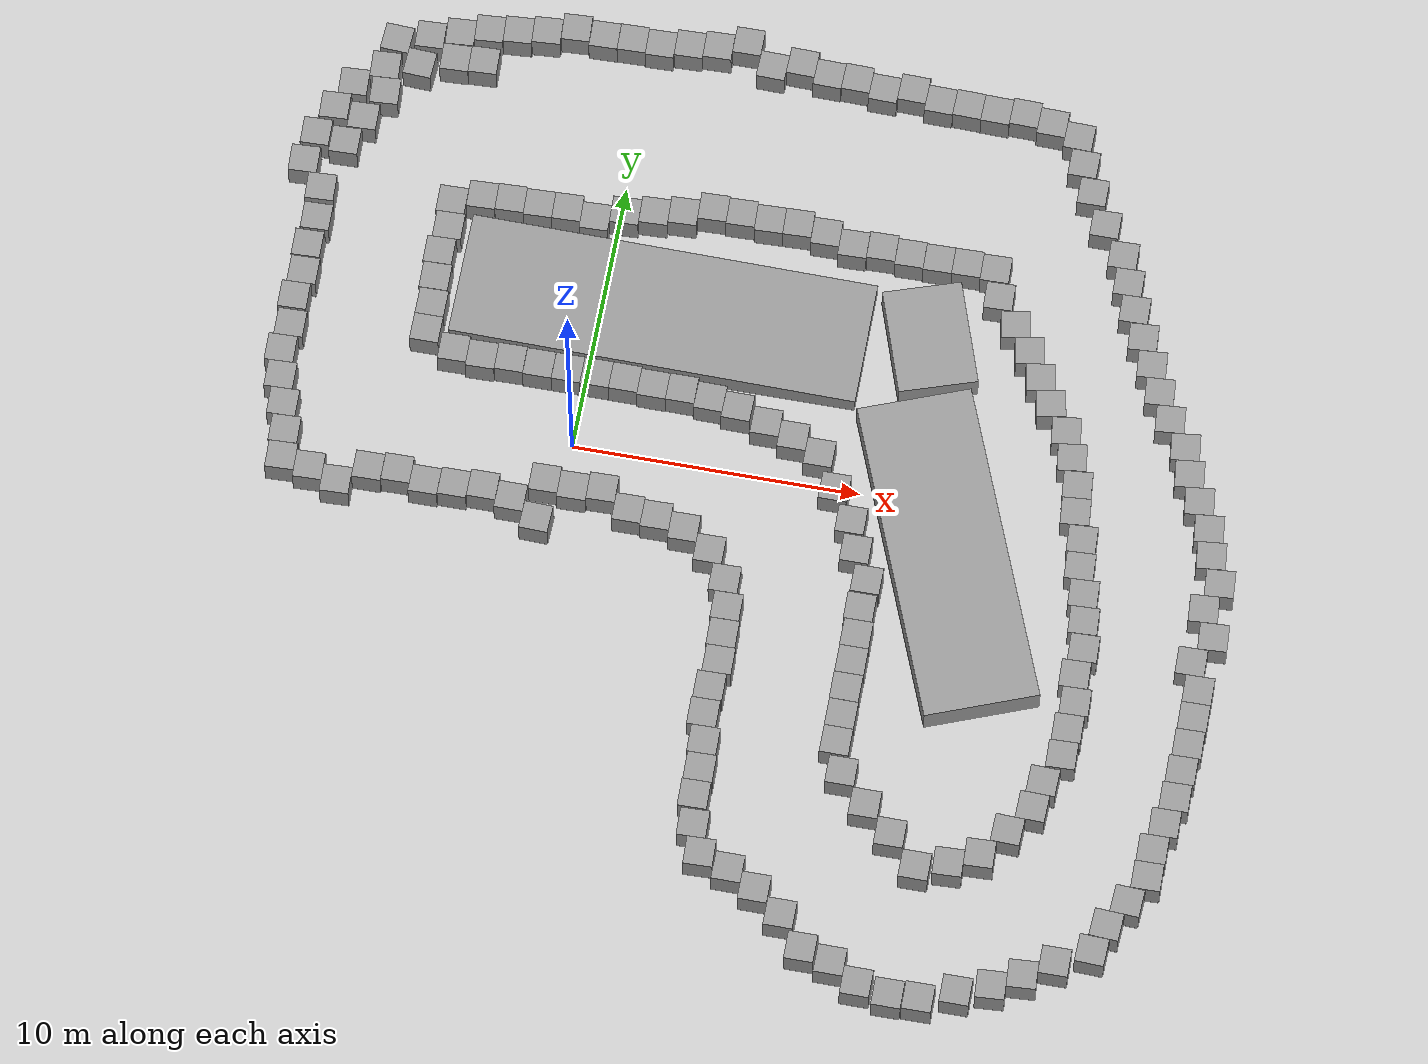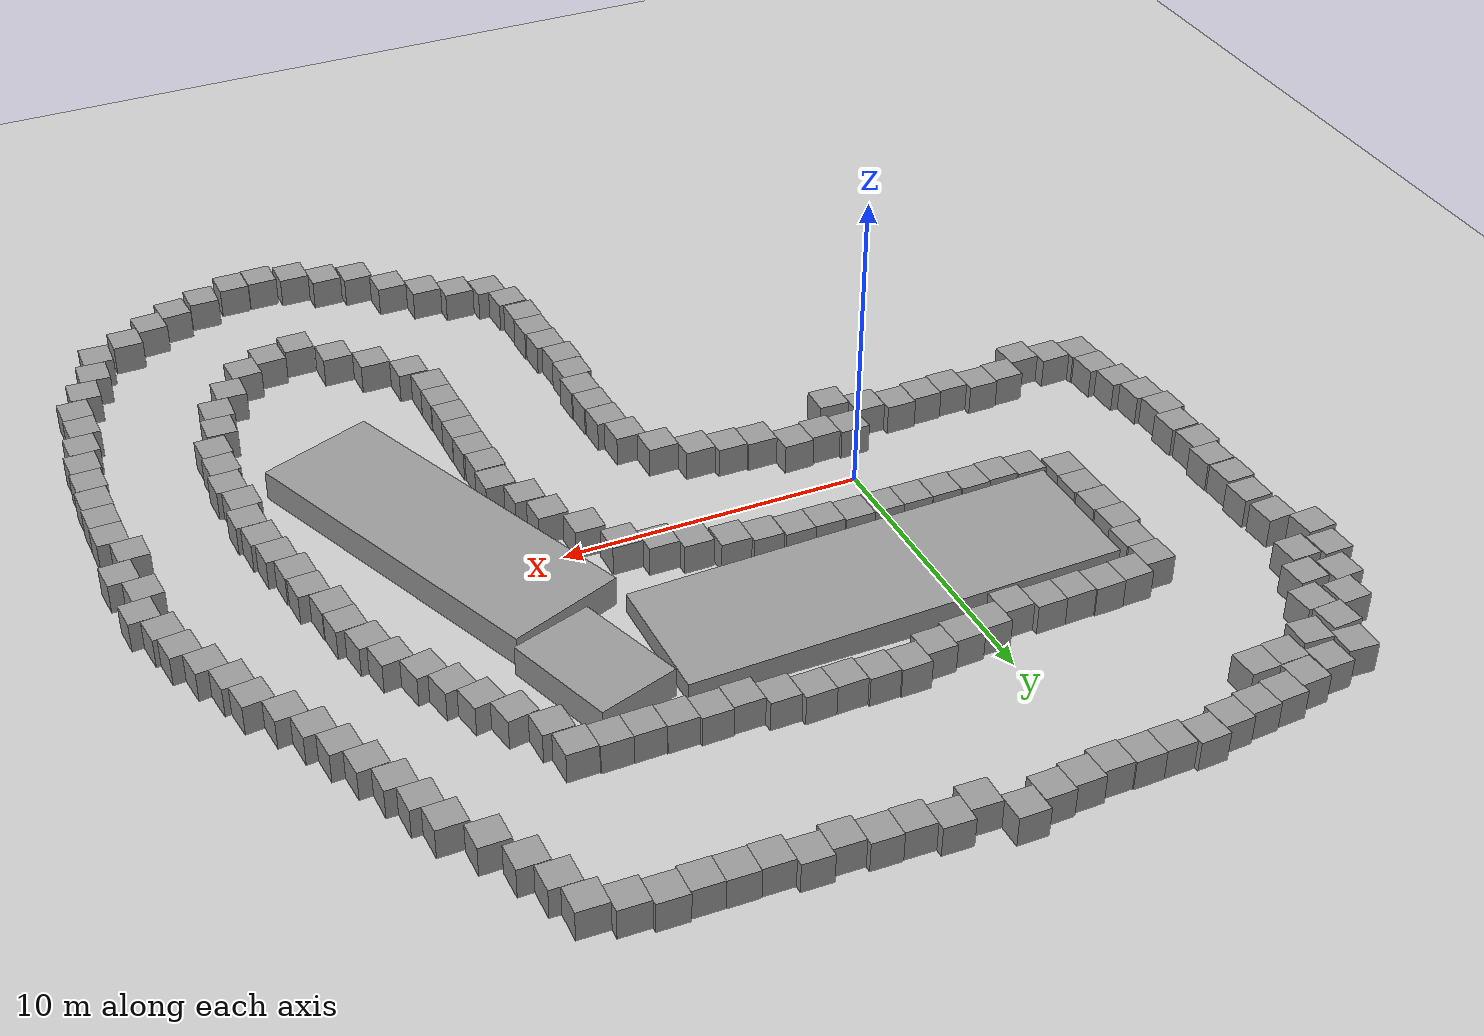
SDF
<sdf version="1.7">
 <world name="default">
  <light name="sun" type="directional">
   <pose>0 0 10 0 -0 0</pose>
   <diffuse>0.8 0.8 0.8 1</diffuse>
   <specular>0.2 0.2 0.2 1</specular>
   <attenuation>
    <range>1000</range>
    <constant>0.9</constant>
    <linear>0.01</linear>
    <quadratic>0.001</quadratic>
   </attenuation>
   <direction>-0.5 0.1 -0.9</direction>
   <spot><inner_angle>0</inner_angle><outer_angle>0</outer_angle><falloff>0</falloff></spot>
  </light>
  <model name="ground_plane">
   <static>1</static>
   <link name="link">
    <collision name="collision">
     <geometry><plane><normal>0 0 1</normal><size>100 100</size></plane></geometry>
     <surface>
      <contact><collide_bitmask>65535</collide_bitmask></contact>
      <friction><ode><mu>100</mu><mu2>50</mu2></ode></friction>
     </surface>
    </collision>
    <visual name="visual">
     <cast_shadows>0</cast_shadows>
     <geometry><plane><normal>0 0 1</normal><size>100 100</size></plane></geometry>
     <material>
      <script><uri>file://media/materials/scripts/gazebo.material</uri><name>Gazebo/Grey</name></script>
     </material>
    </visual>
   </link>
  </model>
  <gravity>0 0 -9.8</gravity>
  <magnetic_field>6e-06 2.3e-05 -4.2e-05</magnetic_field>
  <atmosphere type="adiabatic"/>
  <physics type="ode">
   <max_step_size>0.001</max_step_size>
   <real_time_factor>1</real_time_factor>
   <real_time_update_rate>1000</real_time_update_rate>
  </physics>
  <scene><ambient>0.4 0.4 0.4 1</ambient><background>0.7 0.7 0.7 1</background><shadows>1</shadows></scene>
  <spherical_coordinates>
   <surface_model>EARTH_WGS84</surface_model>
   <latitude_deg>0</latitude_deg>
   <longitude_deg>0</longitude_deg>
   <elevation>0</elevation>
   <heading_deg>0</heading_deg>
  </spherical_coordinates>
  <model name="unit_box">
   <pose>-1.6306 2.48148 0.5 0 -0 0.003919</pose>
   <link name="link">
    <inertial>
     <mass>1</mass>
     <inertia>
      <ixx>0.166667</ixx>
      <ixy>0</ixy>
      <ixz>0</ixz>
      <iyy>0.166667</iyy>
      <iyz>0</iyz>
      <izz>0.166667</izz>
     </inertia>
    </inertial>
    <collision name="collision"><geometry><box><size>1 1 1</size></box></geometry></collision>
    <visual name="visual">
     <geometry><box><size>1 1 1</size></box></geometry>
     <material>
      <script><name>Gazebo/Grey</name><uri>file://media/materials/scripts/gazebo.material</uri></script>
     </material>
    </visual>
   </link>
  </model>
  <model name="unit_box_0">
   <pose>-0.627463 2.48304 0.5 0 0 -0.002213</pose>
   <link name="link">
    <inertial>
     <mass>1</mass>
     <inertia>
      <ixx>0.166667</ixx>
      <ixy>0</ixy>
      <ixz>0</ixz>
      <iyy>0.166667</iyy>
      <iyz>0</iyz>
      <izz>0.166667</izz>
     </inertia>
    </inertial>
    <collision name="collision"><geometry><box><size>1 1 1</size></box></geometry></collision>
    <visual name="visual">
     <geometry><box><size>1 1 1</size></box></geometry>
     <material>
      <script><name>Gazebo/Grey</name><uri>file://media/materials/scripts/gazebo.material</uri></script>
     </material>
    </visual>
   </link>
  </model>
  <model name="unit_box_1">
   <pose>0.372536 2.48136 0.5 0 0 -0.002213</pose>
   <link name="link">
    <inertial>
     <mass>1</mass>
     <inertia>
      <ixx>0.166667</ixx>
      <ixy>0</ixy>
      <ixz>0</ixz>
      <iyy>0.166667</iyy>
      <iyz>0</iyz>
      <izz>0.166667</izz>
     </inertia>
    </inertial>
    <collision name="collision"><geometry><box><size>1 1 1</size></box></geometry></collision>
    <visual name="visual">
     <geometry><box><size>1 1 1</size></box></geometry>
     <material>
      <script><name>Gazebo/Grey</name><uri>file://media/materials/scripts/gazebo.material</uri></script>
     </material>
    </visual>
   </link>
  </model>
  <model name="unit_box_2">
   <pose>1.37261 2.47906 0.5 0 0 -0.002082</pose>
   <link name="link">
    <inertial>
     <mass>1</mass>
     <inertia>
      <ixx>0.166667</ixx>
      <ixy>0</ixy>
      <ixz>0</ixz>
      <iyy>0.166667</iyy>
      <iyz>0</iyz>
      <izz>0.166667</izz>
     </inertia>
    </inertial>
    <collision name="collision"><geometry><box><size>1 1 1</size></box></geometry></collision>
    <visual name="visual">
     <geometry><box><size>1 1 1</size></box></geometry>
     <material>
      <script><name>Gazebo/Grey</name><uri>file://media/materials/scripts/gazebo.material</uri></script>
     </material>
    </visual>
   </link>
  </model>
  <model name="unit_box_3">
   <pose>2.37253 2.41076 0.5 0 -0 -0.001967</pose>
   <link name="link">
    <inertial>
     <mass>1</mass>
     <inertia>
      <ixx>0.166667</ixx>
      <ixy>0</ixy>
      <ixz>0</ixz>
      <iyy>0.166667</iyy>
      <iyz>0</iyz>
      <izz>0.166667</izz>
     </inertia>
    </inertial>
    <collision name="collision"><geometry><box><size>1 1 1</size></box></geometry></collision>
    <visual name="visual">
     <geometry><box><size>1 1 1</size></box></geometry>
     <material>
      <script><name>Gazebo/Grey</name><uri>file://media/materials/scripts/gazebo.material</uri></script>
     </material>
    </visual>
   </link>
  </model>
  <model name="unit_box_4">
   <pose>3.37256 2.4173 0.5 0 -0 -0.00193</pose>
   <link name="link">
    <inertial>
     <mass>1</mass>
     <inertia>
      <ixx>0.166667</ixx>
      <ixy>0</ixy>
      <ixz>0</ixz>
      <iyy>0.166667</iyy>
      <iyz>0</iyz>
      <izz>0.166667</izz>
     </inertia>
    </inertial>
    <collision name="collision"><geometry><box><size>1 1 1</size></box></geometry></collision>
    <visual name="visual">
     <geometry><box><size>1 1 1</size></box></geometry>
     <material>
      <script><name>Gazebo/Grey</name><uri>file://media/materials/scripts/gazebo.material</uri></script>
     </material>
    </visual>
   </link>
  </model>
  <model name="unit_box_5">
   <pose>-1.63227 -2.63169 0.5 0 0 -0.008028</pose>
   <link name="link">
    <inertial>
     <mass>1</mass>
     <inertia>
      <ixx>0.166667</ixx>
      <ixy>0</ixy>
      <ixz>0</ixz>
      <iyy>0.166667</iyy>
      <iyz>0</iyz>
      <izz>0.166667</izz>
     </inertia>
    </inertial>
    <collision name="collision"><geometry><box><size>1 1 1</size></box></geometry></collision>
    <visual name="visual">
     <geometry><box><size>1 1 1</size></box></geometry>
     <material>
      <script><name>Gazebo/Grey</name><uri>file://media/materials/scripts/gazebo.material</uri></script>
     </material>
    </visual>
   </link>
  </model>
  <model name="unit_box_6">
   <pose>-2.63556 2.50705 0.5 0 -0 0.012705</pose>
   <link name="link">
    <inertial>
     <mass>1</mass>
     <inertia>
      <ixx>0.166667</ixx>
      <ixy>0</ixy>
      <ixz>0</ixz>
      <iyy>0.166667</iyy>
      <iyz>0</iyz>
      <izz>0.166667</izz>
     </inertia>
    </inertial>
    <collision name="collision"><geometry><box><size>1 1 1</size></box></geometry></collision>
    <visual name="visual">
     <geometry><box><size>1 1 1</size></box></geometry>
     <material>
      <script><name>Gazebo/Grey</name><uri>file://media/materials/scripts/gazebo.material</uri></script>
     </material>
    </visual>
   </link>
  </model>
  <model name="unit_box_7">
   <pose>-3.63502 2.45258 0.5 0 -0 0.012608</pose>
   <link name="link">
    <inertial>
     <mass>1</mass>
     <inertia>
      <ixx>0.166667</ixx>
      <ixy>0</ixy>
      <ixz>0</ixz>
      <iyy>0.166667</iyy>
      <iyz>0</iyz>
      <izz>0.166667</izz>
     </inertia>
    </inertial>
    <collision name="collision"><geometry><box><size>1 1 1</size></box></geometry></collision>
    <visual name="visual">
     <geometry><box><size>1 1 1</size></box></geometry>
     <material>
      <script><name>Gazebo/Grey</name><uri>file://media/materials/scripts/gazebo.material</uri></script>
     </material>
    </visual>
   </link>
  </model>
  <model name="unit_box_8">
   <pose>-4.63656 2.54261 0.5 0 -0 0.011882</pose>
   <link name="link">
    <inertial>
     <mass>1</mass>
     <inertia>
      <ixx>0.166667</ixx>
      <ixy>0</ixy>
      <ixz>0</ixz>
      <iyy>0.166667</iyy>
      <iyz>0</iyz>
      <izz>0.166667</izz>
     </inertia>
    </inertial>
    <collision name="collision"><geometry><box><size>1 1 1</size></box></geometry></collision>
    <visual name="visual">
     <geometry><box><size>1 1 1</size></box></geometry>
     <material>
      <script><name>Gazebo/Grey</name><uri>file://media/materials/scripts/gazebo.material</uri></script>
     </material>
    </visual>
   </link>
  </model>
  <model name="unit_box_9">
   <pose>-2.63745 -2.38465 0.5 0 -0 0.002465</pose>
   <link name="link">
    <inertial>
     <mass>1</mass>
     <inertia>
      <ixx>0.166667</ixx>
      <ixy>0</ixy>
      <ixz>0</ixz>
      <iyy>0.166667</iyy>
      <iyz>0</iyz>
      <izz>0.166667</izz>
     </inertia>
    </inertial>
    <collision name="collision"><geometry><box><size>1 1 1</size></box></geometry></collision>
    <visual name="visual">
     <geometry><box><size>1 1 1</size></box></geometry>
     <material>
      <script><name>Gazebo/Grey</name><uri>file://media/materials/scripts/gazebo.material</uri></script>
     </material>
    </visual>
   </link>
  </model>
  <model name="unit_box_10">
   <pose>-3.63746 -2.49021 0.5 0 -0 0.003056</pose>
   <link name="link">
    <inertial>
     <mass>1</mass>
     <inertia>
      <ixx>0.166667</ixx>
      <ixy>0</ixy>
      <ixz>0</ixz>
      <iyy>0.166667</iyy>
      <iyz>0</iyz>
      <izz>0.166667</izz>
     </inertia>
    </inertial>
    <collision name="collision"><geometry><box><size>1 1 1</size></box></geometry></collision>
    <visual name="visual">
     <geometry><box><size>1 1 1</size></box></geometry>
     <material>
      <script><name>Gazebo/Grey</name><uri>file://media/materials/scripts/gazebo.material</uri></script>
     </material>
    </visual>
   </link>
  </model>
  <model name="unit_box_11">
   <pose>-0.613582 -1.75543 0.5 0 -0 0.017531</pose>
   <link name="link">
    <inertial>
     <mass>1</mass>
     <inertia>
      <ixx>0.166667</ixx>
      <ixy>0</ixy>
      <ixz>0</ixz>
      <iyy>0.166667</iyy>
      <iyz>0</iyz>
      <izz>0.166667</izz>
     </inertia>
    </inertial>
    <collision name="collision"><geometry><box><size>1 1 1</size></box></geometry></collision>
    <visual name="visual">
     <geometry><box><size>1 1 1</size></box></geometry>
     <material>
      <script><name>Gazebo/Grey</name><uri>file://media/materials/scripts/gazebo.material</uri></script>
     </material>
    </visual>
   </link>
  </model>
  <model name="unit_box_12">
   <pose>0.388434 -1.86074 0.499995 0 -1e-05 0.01748</pose>
   <link name="link">
    <inertial>
     <mass>1</mass>
     <inertia>
      <ixx>0.166667</ixx>
      <ixy>0</ixy>
      <ixz>0</ixz>
      <iyy>0.166667</iyy>
      <iyz>0</iyz>
      <izz>0.166667</izz>
     </inertia>
    </inertial>
    <collision name="collision"><geometry><box><size>1 1 1</size></box></geometry></collision>
    <visual name="visual">
     <geometry><box><size>1 1 1</size></box></geometry>
     <material>
      <script><name>Gazebo/Grey</name><uri>file://media/materials/scripts/gazebo.material</uri></script>
     </material>
    </visual>
   </link>
  </model>
  <model name="unit_box_13">
   <pose>1.3866 -1.74674 0.5 0 -0 0.017478</pose>
   <link name="link">
    <inertial>
     <mass>1</mass>
     <inertia>
      <ixx>0.166667</ixx>
      <ixy>0</ixy>
      <ixz>0</ixz>
      <iyy>0.166667</iyy>
      <iyz>0</iyz>
      <izz>0.166667</izz>
     </inertia>
    </inertial>
    <collision name="collision"><geometry><box><size>1 1 1</size></box></geometry></collision>
    <visual name="visual">
     <geometry><box><size>1 1 1</size></box></geometry>
     <material>
      <script><name>Gazebo/Grey</name><uri>file://media/materials/scripts/gazebo.material</uri></script>
     </material>
    </visual>
   </link>
  </model>
  <model name="unit_box_14">
   <pose>2.39599 -2.35304 0.5 0 -0 0.006262</pose>
   <link name="link">
    <inertial>
     <mass>1</mass>
     <inertia>
      <ixx>0.166667</ixx>
      <ixy>0</ixy>
      <ixz>0</ixz>
      <iyy>0.166667</iyy>
      <iyz>0</iyz>
      <izz>0.166667</izz>
     </inertia>
    </inertial>
    <collision name="collision"><geometry><box><size>1 1 1</size></box></geometry></collision>
    <visual name="visual">
     <geometry><box><size>1 1 1</size></box></geometry>
     <material>
      <script><name>Gazebo/Grey</name><uri>file://media/materials/scripts/gazebo.material</uri></script>
     </material>
    </visual>
   </link>
  </model>
  <model name="unit_box_15">
   <pose>3.39655 -2.43483 0.5 0 -0 0.006225</pose>
   <link name="link">
    <inertial>
     <mass>1</mass>
     <inertia>
      <ixx>0.166667</ixx>
      <ixy>0</ixy>
      <ixz>0</ixz>
      <iyy>0.166667</iyy>
      <iyz>0</iyz>
      <izz>0.166667</izz>
     </inertia>
    </inertial>
    <collision name="collision"><geometry><box><size>1 1 1</size></box></geometry></collision>
    <visual name="visual">
     <geometry><box><size>1 1 1</size></box></geometry>
     <material>
      <script><name>Gazebo/Grey</name><uri>file://media/materials/scripts/gazebo.material</uri></script>
     </material>
    </visual>
   </link>
  </model>
  <model name="unit_box_16">
   <pose>4.39824 -2.70244 0.499995 -1e-05 -0 0.006225</pose>
   <link name="link">
    <inertial>
     <mass>1</mass>
     <inertia>
      <ixx>0.166667</ixx>
      <ixy>0</ixy>
      <ixz>0</ixz>
      <iyy>0.166667</iyy>
      <iyz>0</iyz>
      <izz>0.166667</izz>
     </inertia>
    </inertial>
    <collision name="collision"><geometry><box><size>1 1 1</size></box></geometry></collision>
    <visual name="visual">
     <geometry><box><size>1 1 1</size></box></geometry>
     <material>
      <script><name>Gazebo/Grey</name><uri>file://media/materials/scripts/gazebo.material</uri></script>
     </material>
    </visual>
   </link>
  </model>
  <model name="unit_box_17">
   <pose>5.40235 -3.34785 0.5 0 -0 0.006364</pose>
   <link name="link">
    <inertial>
     <mass>1</mass>
     <inertia>
      <ixx>0.166667</ixx>
      <ixy>0</ixy>
      <ixz>0</ixz>
      <iyy>0.166667</iyy>
      <iyz>0</iyz>
      <izz>0.166667</izz>
     </inertia>
    </inertial>
    <collision name="collision"><geometry><box><size>1 1 1</size></box></geometry></collision>
    <visual name="visual">
     <geometry><box><size>1 1 1</size></box></geometry>
     <material>
      <script><name>Gazebo/Grey</name><uri>file://media/materials/scripts/gazebo.material</uri></script>
     </material>
    </visual>
   </link>
  </model>
  <model name="unit_box_18">
   <pose>6.11715 -4.34222 0.5 0 -0 0.011712</pose>
   <link name="link">
    <inertial>
     <mass>1</mass>
     <inertia>
      <ixx>0.166667</ixx>
      <ixy>0</ixy>
      <ixz>0</ixz>
      <iyy>0.166667</iyy>
      <iyz>0</iyz>
      <izz>0.166667</izz>
     </inertia>
    </inertial>
    <collision name="collision"><geometry><box><size>1 1 1</size></box></geometry></collision>
    <visual name="visual">
     <geometry><box><size>1 1 1</size></box></geometry>
     <material>
      <script><name>Gazebo/Grey</name><uri>file://media/materials/scripts/gazebo.material</uri></script>
     </material>
    </visual>
   </link>
  </model>
  <model name="unit_box_19">
   <pose>6.3639 -5.3397 0.5 0 -0 0.011886</pose>
   <link name="link">
    <inertial>
     <mass>1</mass>
     <inertia>
      <ixx>0.166667</ixx>
      <ixy>0</ixy>
      <ixz>0</ixz>
      <iyy>0.166667</iyy>
      <iyz>0</iyz>
      <izz>0.166667</izz>
     </inertia>
    </inertial>
    <collision name="collision"><geometry><box><size>1 1 1</size></box></geometry></collision>
    <visual name="visual">
     <geometry><box><size>1 1 1</size></box></geometry>
     <material>
      <script><name>Gazebo/Grey</name><uri>file://media/materials/scripts/gazebo.material</uri></script>
     </material>
    </visual>
   </link>
  </model>
  <model name="unit_box_20">
   <pose>4.38108 2.28354 0.5 0 0 -0.015499</pose>
   <link name="link">
    <inertial>
     <mass>1</mass>
     <inertia>
      <ixx>0.166667</ixx>
      <ixy>0</ixy>
      <ixz>0</ixz>
      <iyy>0.166667</iyy>
      <iyz>0</iyz>
      <izz>0.166667</izz>
     </inertia>
    </inertial>
    <collision name="collision"><geometry><box><size>1 1 1</size></box></geometry></collision>
    <visual name="visual">
     <geometry><box><size>1 1 1</size></box></geometry>
     <material>
      <script><name>Gazebo/Grey</name><uri>file://media/materials/scripts/gazebo.material</uri></script>
     </material>
    </visual>
   </link>
  </model>
  <model name="unit_box_21">
   <pose>5.37841 2.09652 0.5 -0 -0 -0.0155</pose>
   <link name="link">
    <inertial>
     <mass>1</mass>
     <inertia>
      <ixx>0.166667</ixx>
      <ixy>0</ixy>
      <ixz>0</ixz>
      <iyy>0.166667</iyy>
      <iyz>0</iyz>
      <izz>0.166667</izz>
     </inertia>
    </inertial>
    <collision name="collision"><geometry><box><size>1 1 1</size></box></geometry></collision>
    <visual name="visual">
     <geometry><box><size>1 1 1</size></box></geometry>
     <material>
      <script><name>Gazebo/Grey</name><uri>file://media/materials/scripts/gazebo.material</uri></script>
     </material>
    </visual>
   </link>
  </model>
  <model name="unit_box_22">
   <pose>6.44585 1.71085 0.5 0 -0 5e-06</pose>
   <link name="link">
    <inertial>
     <mass>1</mass>
     <inertia>
      <ixx>0.166667</ixx>
      <ixy>0</ixy>
      <ixz>0</ixz>
      <iyy>0.166667</iyy>
      <iyz>0</iyz>
      <izz>0.166667</izz>
     </inertia>
    </inertial>
    <collision name="collision"><geometry><box><size>1 1 1</size></box></geometry></collision>
    <visual name="visual">
     <geometry><box><size>1 1 1</size></box></geometry>
     <material>
      <script><name>Gazebo/Grey</name><uri>file://media/materials/scripts/gazebo.material</uri></script>
     </material>
    </visual>
   </link>
  </model>
  <model name="unit_box_23">
   <pose>7.4465 1.3632 0.5 0 -0 5e-06</pose>
   <link name="link">
    <inertial>
     <mass>1</mass>
     <inertia>
      <ixx>0.166667</ixx>
      <ixy>0</ixy>
      <ixz>0</ixz>
      <iyy>0.166667</iyy>
      <iyz>0</iyz>
      <izz>0.166667</izz>
     </inertia>
    </inertial>
    <collision name="collision"><geometry><box><size>1 1 1</size></box></geometry></collision>
    <visual name="visual">
     <geometry><box><size>1 1 1</size></box></geometry>
     <material>
      <script><name>Gazebo/Grey</name><uri>file://media/materials/scripts/gazebo.material</uri></script>
     </material>
    </visual>
   </link>
  </model>
  <model name="unit_box_24">
   <pose>8.44685 0.885148 0.5 0 -0 5e-06</pose>
   <link name="link">
    <inertial>
     <mass>1</mass>
     <inertia>
      <ixx>0.166667</ixx>
      <ixy>0</ixy>
      <ixz>0</ixz>
      <iyy>0.166667</iyy>
      <iyz>0</iyz>
      <izz>0.166667</izz>
     </inertia>
    </inertial>
    <collision name="collision"><geometry><box><size>1 1 1</size></box></geometry></collision>
    <visual name="visual">
     <geometry><box><size>1 1 1</size></box></geometry>
     <material>
      <script><name>Gazebo/Grey</name><uri>file://media/materials/scripts/gazebo.material</uri></script>
     </material>
    </visual>
   </link>
  </model>
  <model name="unit_box_25">
   <pose>9.18636 -0.290445 0.5 0 -0 5e-06</pose>
   <link name="link">
    <inertial>
     <mass>1</mass>
     <inertia>
      <ixx>0.166667</ixx>
      <ixy>0</ixy>
      <ixz>0</ixz>
      <iyy>0.166667</iyy>
      <iyz>0</iyz>
      <izz>0.166667</izz>
     </inertia>
    </inertial>
    <collision name="collision"><geometry><box><size>1 1 1</size></box></geometry></collision>
    <visual name="visual">
     <geometry><box><size>1 1 1</size></box></geometry>
     <material>
      <script><name>Gazebo/Grey</name><uri>file://media/materials/scripts/gazebo.material</uri></script>
     </material>
    </visual>
   </link>
  </model>
  <model name="unit_box_26">
   <pose>9.95453 -1.40481 0.5 0 -0 0.004582</pose>
   <link name="link">
    <inertial>
     <mass>1</mass>
     <inertia>
      <ixx>0.166667</ixx>
      <ixy>0</ixy>
      <ixz>0</ixz>
      <iyy>0.166667</iyy>
      <iyz>0</iyz>
      <izz>0.166667</izz>
     </inertia>
    </inertial>
    <collision name="collision"><geometry><box><size>1 1 1</size></box></geometry></collision>
    <visual name="visual">
     <geometry><box><size>1 1 1</size></box></geometry>
     <material>
      <script><name>Gazebo/Grey</name><uri>file://media/materials/scripts/gazebo.material</uri></script>
     </material>
    </visual>
   </link>
  </model>
  <model name="unit_box_27">
   <pose>10.305 -2.44806 0.5 0 -0 5e-06</pose>
   <link name="link">
    <inertial>
     <mass>1</mass>
     <inertia>
      <ixx>0.166667</ixx>
      <ixy>0</ixy>
      <ixz>0</ixz>
      <iyy>0.166667</iyy>
      <iyz>0</iyz>
      <izz>0.166667</izz>
     </inertia>
    </inertial>
    <collision name="collision"><geometry><box><size>1 1 1</size></box></geometry></collision>
    <visual name="visual">
     <geometry><box><size>1 1 1</size></box></geometry>
     <material>
      <script><name>Gazebo/Grey</name><uri>file://media/materials/scripts/gazebo.material</uri></script>
     </material>
    </visual>
   </link>
  </model>
  <model name="unit_box_28">
   <pose>10.8726 -3.51528 0.5 0 0 -5e-06</pose>
   <link name="link">
    <inertial>
     <mass>1</mass>
     <inertia>
      <ixx>0.166667</ixx>
      <ixy>0</ixy>
      <ixz>0</ixz>
      <iyy>0.166667</iyy>
      <iyz>0</iyz>
      <izz>0.166667</izz>
     </inertia>
    </inertial>
    <collision name="collision"><geometry><box><size>1 1 1</size></box></geometry></collision>
    <visual name="visual">
     <geometry><box><size>1 1 1</size></box></geometry>
     <material>
      <script><name>Gazebo/Grey</name><uri>file://media/materials/scripts/gazebo.material</uri></script>
     </material>
    </visual>
   </link>
  </model>
  <model name="unit_box_29">
   <pose>10.8241 -4.54943 0.5 0 -0 0.000273</pose>
   <link name="link">
    <inertial>
     <mass>1</mass>
     <inertia>
      <ixx>0.166667</ixx>
      <ixy>0</ixy>
      <ixz>0</ixz>
      <iyy>0.166667</iyy>
      <iyz>0</iyz>
      <izz>0.166667</izz>
     </inertia>
    </inertial>
    <collision name="collision"><geometry><box><size>1 1 1</size></box></geometry></collision>
    <visual name="visual">
     <geometry><box><size>1 1 1</size></box></geometry>
     <material>
      <script><name>Gazebo/Grey</name><uri>file://media/materials/scripts/gazebo.material</uri></script>
     </material>
    </visual>
   </link>
  </model>
  <model name="unit_box_30">
   <pose>10.8797 -5.54946 0.5 0 -0 0.00022</pose>
   <link name="link">
    <inertial>
     <mass>1</mass>
     <inertia>
      <ixx>0.166667</ixx>
      <ixy>0</ixy>
      <ixz>0</ixz>
      <iyy>0.166667</iyy>
      <iyz>0</iyz>
      <izz>0.166667</izz>
     </inertia>
    </inertial>
    <collision name="collision"><geometry><box><size>1 1 1</size></box></geometry></collision>
    <visual name="visual">
     <geometry><box><size>1 1 1</size></box></geometry>
     <material>
      <script><name>Gazebo/Grey</name><uri>file://media/materials/scripts/gazebo.material</uri></script>
     </material>
    </visual>
   </link>
  </model>
  <model name="unit_box_31">
   <pose>6.41405 -6.33968 0.5 0 -0 0.012967</pose>
   <link name="link">
    <inertial>
     <mass>1</mass>
     <inertia>
      <ixx>0.166667</ixx>
      <ixy>0</ixy>
      <ixz>0</ixz>
      <iyy>0.166667</iyy>
      <iyz>0</iyz>
      <izz>0.166667</izz>
     </inertia>
    </inertial>
    <collision name="collision"><geometry><box><size>1 1 1</size></box></geometry></collision>
    <visual name="visual">
     <geometry><box><size>1 1 1</size></box></geometry>
     <material>
      <script><name>Gazebo/Grey</name><uri>file://media/materials/scripts/gazebo.material</uri></script>
     </material>
    </visual>
   </link>
  </model>
  <model name="unit_box_32">
   <pose>10.8891 -6.5495 0.5 0 -0 0.00017</pose>
   <link name="link">
    <inertial>
     <mass>1</mass>
     <inertia>
      <ixx>0.166667</ixx>
      <ixy>0</ixy>
      <ixz>0</ixz>
      <iyy>0.166667</iyy>
      <iyz>0</iyz>
      <izz>0.166667</izz>
     </inertia>
    </inertial>
    <collision name="collision"><geometry><box><size>1 1 1</size></box></geometry></collision>
    <visual name="visual">
     <geometry><box><size>1 1 1</size></box></geometry>
     <material>
      <script><name>Gazebo/Grey</name><uri>file://media/materials/scripts/gazebo.material</uri></script>
     </material>
    </visual>
   </link>
  </model>
  <model name="unit_box_33">
   <pose>6.46013 -7.33918 0.5 0 -0 0.01297</pose>
   <link name="link">
    <inertial>
     <mass>1</mass>
     <inertia>
      <ixx>0.166667</ixx>
      <ixy>0</ixy>
      <ixz>0</ixz>
      <iyy>0.166667</iyy>
      <iyz>0</iyz>
      <izz>0.166667</izz>
     </inertia>
    </inertial>
    <collision name="collision"><geometry><box><size>1 1 1</size></box></geometry></collision>
    <visual name="visual">
     <geometry><box><size>1 1 1</size></box></geometry>
     <material>
      <script><name>Gazebo/Grey</name><uri>file://media/materials/scripts/gazebo.material</uri></script>
     </material>
    </visual>
   </link>
  </model>
  <model name="unit_box_32_clone">
   <pose>6.33217 -8.34109 0.5 0 -0 0.013301</pose>
   <link name="link">
    <inertial>
     <mass>1</mass>
     <inertia>
      <ixx>0.166667</ixx>
      <ixy>0</ixy>
      <ixz>0</ixz>
      <iyy>0.166667</iyy>
      <iyz>0</iyz>
      <izz>0.166667</izz>
     </inertia>
    </inertial>
    <collision name="collision"><geometry><box><size>1 1 1</size></box></geometry></collision>
    <visual name="visual">
     <geometry><box><size>1 1 1</size></box></geometry>
     <material>
      <script><name>Gazebo/Grey</name><uri>file://media/materials/scripts/gazebo.material</uri></script>
     </material>
    </visual>
   </link>
  </model>
  <model name="unit_box_32_clone_0">
   <pose>10.8828 -7.54992 0.5 0 0 -0.000395</pose>
   <link name="link">
    <inertial>
     <mass>1</mass>
     <inertia>
      <ixx>0.166667</ixx>
      <ixy>0</ixy>
      <ixz>0</ixz>
      <iyy>0.166667</iyy>
      <iyz>0</iyz>
      <izz>0.166667</izz>
     </inertia>
    </inertial>
    <collision name="collision"><geometry><box><size>1 1 1</size></box></geometry></collision>
    <visual name="visual">
     <geometry><box><size>1 1 1</size></box></geometry>
     <material>
      <script><name>Gazebo/Grey</name><uri>file://media/materials/scripts/gazebo.material</uri></script>
     </material>
    </visual>
   </link>
  </model>
  <model name="unit_box_32_clone_1">
   <pose>6.30854 -9.34159 0.5 0 -0 0.013492</pose>
   <link name="link">
    <inertial>
     <mass>1</mass>
     <inertia>
      <ixx>0.166667</ixx>
      <ixy>0</ixy>
      <ixz>0</ixz>
      <iyy>0.166667</iyy>
      <iyz>0</iyz>
      <izz>0.166667</izz>
     </inertia>
    </inertial>
    <collision name="collision"><geometry><box><size>1 1 1</size></box></geometry></collision>
    <visual name="visual">
     <geometry><box><size>1 1 1</size></box></geometry>
     <material>
      <script><name>Gazebo/Grey</name><uri>file://media/materials/scripts/gazebo.material</uri></script>
     </material>
    </visual>
   </link>
  </model>
  <model name="unit_box_32_clone_2">
   <pose>6.49657 -10.3392 0.5 0 -0 0.013501</pose>
   <link name="link">
    <inertial>
     <mass>1</mass>
     <inertia>
      <ixx>0.166667</ixx>
      <ixy>0</ixy>
      <ixz>0</ixz>
      <iyy>0.166667</iyy>
      <iyz>0</iyz>
      <izz>0.166667</izz>
     </inertia>
    </inertial>
    <collision name="collision"><geometry><box><size>1 1 1</size></box></geometry></collision>
    <visual name="visual">
     <geometry><box><size>1 1 1</size></box></geometry>
     <material>
      <script><name>Gazebo/Grey</name><uri>file://media/materials/scripts/gazebo.material</uri></script>
     </material>
    </visual>
   </link>
  </model>
  <model name="unit_box_32_clone_3">
   <pose>10.8991 -8.55074 0.5 0 0 -0.001861</pose>
   <link name="link">
    <inertial>
     <mass>1</mass>
     <inertia>
      <ixx>0.166667</ixx>
      <ixy>0</ixy>
      <ixz>0</ixz>
      <iyy>0.166667</iyy>
      <iyz>0</iyz>
      <izz>0.166667</izz>
     </inertia>
    </inertial>
    <collision name="collision"><geometry><box><size>1 1 1</size></box></geometry></collision>
    <visual name="visual">
     <geometry><box><size>1 1 1</size></box></geometry>
     <material>
      <script><name>Gazebo/Grey</name><uri>file://media/materials/scripts/gazebo.material</uri></script>
     </material>
    </visual>
   </link>
  </model>
  <model name="unit_box_32_clone_4">
   <pose>10.8972 -9.55128 0.5 0 0 -0.002928</pose>
   <link name="link">
    <inertial>
     <mass>1</mass>
     <inertia>
      <ixx>0.166667</ixx>
      <ixy>0</ixy>
      <ixz>0</ixz>
      <iyy>0.166667</iyy>
      <iyz>0</iyz>
      <izz>0.166667</izz>
     </inertia>
    </inertial>
    <collision name="collision"><geometry><box><size>1 1 1</size></box></geometry></collision>
    <visual name="visual">
     <geometry><box><size>1 1 1</size></box></geometry>
     <material>
      <script><name>Gazebo/Grey</name><uri>file://media/materials/scripts/gazebo.material</uri></script>
     </material>
    </visual>
   </link>
  </model>
  <model name="unit_box_32_clone_5">
   <pose>6.55508 -11.3385 0.5 0 -0 0.013518</pose>
   <link name="link">
    <inertial>
     <mass>1</mass>
     <inertia>
      <ixx>0.166667</ixx>
      <ixy>0</ixy>
      <ixz>0</ixz>
      <iyy>0.166667</iyy>
      <iyz>0</iyz>
      <izz>0.166667</izz>
     </inertia>
    </inertial>
    <collision name="collision"><geometry><box><size>1 1 1</size></box></geometry></collision>
    <visual name="visual">
     <geometry><box><size>1 1 1</size></box></geometry>
     <material>
      <script><name>Gazebo/Grey</name><uri>file://media/materials/scripts/gazebo.material</uri></script>
     </material>
    </visual>
   </link>
  </model>
  <model name="unit_box_32_clone_6">
   <pose>11.276 -10.6109 0.5 0 -0 0.001319</pose>
   <link name="link">
    <inertial>
     <mass>1</mass>
     <inertia>
      <ixx>0.166667</ixx>
      <ixy>0</ixy>
      <ixz>0</ixz>
      <iyy>0.166667</iyy>
      <iyz>0</iyz>
      <izz>0.166667</izz>
     </inertia>
    </inertial>
    <collision name="collision"><geometry><box><size>1 1 1</size></box></geometry></collision>
    <visual name="visual">
     <geometry><box><size>1 1 1</size></box></geometry>
     <material>
      <script><name>Gazebo/Grey</name><uri>file://media/materials/scripts/gazebo.material</uri></script>
     </material>
    </visual>
   </link>
  </model>
  <model name="unit_box_32_clone_7">
   <pose>12.2553 -11.6331 0.5 0 -0 0.001319</pose>
   <link name="link">
    <inertial>
     <mass>1</mass>
     <inertia>
      <ixx>0.166667</ixx>
      <ixy>0</ixy>
      <ixz>0</ixz>
      <iyy>0.166667</iyy>
      <iyz>0</iyz>
      <izz>0.166667</izz>
     </inertia>
    </inertial>
    <collision name="collision"><geometry><box><size>1 1 1</size></box></geometry></collision>
    <visual name="visual">
     <geometry><box><size>1 1 1</size></box></geometry>
     <material>
      <script><name>Gazebo/Grey</name><uri>file://media/materials/scripts/gazebo.material</uri></script>
     </material>
    </visual>
   </link>
  </model>
  <model name="unit_box_32_clone_8">
   <pose>13.2773 -12.5272 0.5 0 -0 0.001319</pose>
   <link name="link">
    <inertial>
     <mass>1</mass>
     <inertia>
      <ixx>0.166667</ixx>
      <ixy>0</ixy>
      <ixz>0</ixz>
      <iyy>0.166667</iyy>
      <iyz>0</iyz>
      <izz>0.166667</izz>
     </inertia>
    </inertial>
    <collision name="collision"><geometry><box><size>1 1 1</size></box></geometry></collision>
    <visual name="visual">
     <geometry><box><size>1 1 1</size></box></geometry>
     <material>
      <script><name>Gazebo/Grey</name><uri>file://media/materials/scripts/gazebo.material</uri></script>
     </material>
    </visual>
   </link>
  </model>
  <model name="unit_box_32_clone_9">
   <pose>14.2987 -13.549 0.5 0 -0 0.001319</pose>
   <link name="link">
    <inertial>
     <mass>1</mass>
     <inertia>
      <ixx>0.166667</ixx>
      <ixy>0</ixy>
      <ixz>0</ixz>
      <iyy>0.166667</iyy>
      <iyz>0</iyz>
      <izz>0.166667</izz>
     </inertia>
    </inertial>
    <collision name="collision"><geometry><box><size>1 1 1</size></box></geometry></collision>
    <visual name="visual">
     <geometry><box><size>1 1 1</size></box></geometry>
     <material>
      <script><name>Gazebo/Grey</name><uri>file://media/materials/scripts/gazebo.material</uri></script>
     </material>
    </visual>
   </link>
  </model>
  <model name="unit_box_32_clone_10">
   <pose>15.3803 -13.2281 0.5 0 -0 0.040936</pose>
   <link name="link">
    <inertial>
     <mass>1</mass>
     <inertia>
      <ixx>0.166667</ixx>
      <ixy>0</ixy>
      <ixz>0</ixz>
      <iyy>0.166667</iyy>
      <iyz>0</iyz>
      <izz>0.166667</izz>
     </inertia>
    </inertial>
    <collision name="collision"><geometry><box><size>1 1 1</size></box></geometry></collision>
    <visual name="visual">
     <geometry><box><size>1 1 1</size></box></geometry>
     <material>
      <script><name>Gazebo/Grey</name><uri>file://media/materials/scripts/gazebo.material</uri></script>
     </material>
    </visual>
   </link>
  </model>
  <model name="unit_box_32_clone_11">
   <pose>16.3621 -12.7297 0.5 0 -0 0.038196</pose>
   <link name="link">
    <inertial>
     <mass>1</mass>
     <inertia>
      <ixx>0.166667</ixx>
      <ixy>0</ixy>
      <ixz>0</ixz>
      <iyy>0.166667</iyy>
      <iyz>0</iyz>
      <izz>0.166667</izz>
     </inertia>
    </inertial>
    <collision name="collision"><geometry><box><size>1 1 1</size></box></geometry></collision>
    <visual name="visual">
     <geometry><box><size>1 1 1</size></box></geometry>
     <material>
      <script><name>Gazebo/Grey</name><uri>file://media/materials/scripts/gazebo.material</uri></script>
     </material>
    </visual>
   </link>
  </model>
  <model name="unit_box_32_clone_12">
   <pose>17.1342 -11.7208 0.5 0 -0 -0.034855</pose>
   <link name="link">
    <inertial>
     <mass>1</mass>
     <inertia>
      <ixx>0.166667</ixx>
      <ixy>0</ixy>
      <ixz>0</ixz>
      <iyy>0.166667</iyy>
      <iyz>0</iyz>
      <izz>0.166667</izz>
     </inertia>
    </inertial>
    <collision name="collision"><geometry><box><size>1 1 1</size></box></geometry></collision>
    <visual name="visual">
     <geometry><box><size>1 1 1</size></box></geometry>
     <material>
      <script><name>Gazebo/Grey</name><uri>file://media/materials/scripts/gazebo.material</uri></script>
     </material>
    </visual>
   </link>
  </model>
  <model name="unit_box_32_clone_13">
   <pose>17.8095 -10.7409 0.5 0 0 -0.029257</pose>
   <link name="link">
    <inertial>
     <mass>1</mass>
     <inertia>
      <ixx>0.166667</ixx>
      <ixy>0</ixy>
      <ixz>0</ixz>
      <iyy>0.166667</iyy>
      <iyz>0</iyz>
      <izz>0.166667</izz>
     </inertia>
    </inertial>
    <collision name="collision"><geometry><box><size>1 1 1</size></box></geometry></collision>
    <visual name="visual">
     <geometry><box><size>1 1 1</size></box></geometry>
     <material>
      <script><name>Gazebo/Grey</name><uri>file://media/materials/scripts/gazebo.material</uri></script>
     </material>
    </visual>
   </link>
  </model>
  <model name="unit_box_32_clone_14">
   <pose>18.0046 -9.74617 0.5 0 0 -0.029231</pose>
   <link name="link">
    <inertial>
     <mass>1</mass>
     <inertia>
      <ixx>0.166667</ixx>
      <ixy>0</ixy>
      <ixz>0</ixz>
      <iyy>0.166667</iyy>
      <iyz>0</iyz>
      <izz>0.166667</izz>
     </inertia>
    </inertial>
    <collision name="collision"><geometry><box><size>1 1 1</size></box></geometry></collision>
    <visual name="visual">
     <geometry><box><size>1 1 1</size></box></geometry>
     <material>
      <script><name>Gazebo/Grey</name><uri>file://media/materials/scripts/gazebo.material</uri></script>
     </material>
    </visual>
   </link>
  </model>
  <model name="unit_box_32_clone_15">
   <pose>18.4737 -8.69085 0.5 0 -0 0.024066</pose>
   <link name="link">
    <inertial>
     <mass>1</mass>
     <inertia>
      <ixx>0.166667</ixx>
      <ixy>0</ixy>
      <ixz>0</ixz>
      <iyy>0.166667</iyy>
      <iyz>0</iyz>
      <izz>0.166667</izz>
     </inertia>
    </inertial>
    <collision name="collision"><geometry><box><size>1 1 1</size></box></geometry></collision>
    <visual name="visual">
     <geometry><box><size>1 1 1</size></box></geometry>
     <material>
      <script><name>Gazebo/Grey</name><uri>file://media/materials/scripts/gazebo.material</uri></script>
     </material>
    </visual>
   </link>
  </model>
  <model name="unit_box_32_clone_16">
   <pose>18.5018 -7.68973 0.5 0 -0 0.024358</pose>
   <link name="link">
    <inertial>
     <mass>1</mass>
     <inertia>
      <ixx>0.166667</ixx>
      <ixy>0</ixy>
      <ixz>0</ixz>
      <iyy>0.166667</iyy>
      <iyz>0</iyz>
      <izz>0.166667</izz>
     </inertia>
    </inertial>
    <collision name="collision"><geometry><box><size>1 1 1</size></box></geometry></collision>
    <visual name="visual">
     <geometry><box><size>1 1 1</size></box></geometry>
     <material>
      <script><name>Gazebo/Grey</name><uri>file://media/materials/scripts/gazebo.material</uri></script>
     </material>
    </visual>
   </link>
  </model>
  <model name="unit_box_32_clone_17">
   <pose>18.5887 -6.68717 0.5 0 -0 0.024653</pose>
   <link name="link">
    <inertial>
     <mass>1</mass>
     <inertia>
      <ixx>0.166667</ixx>
      <ixy>0</ixy>
      <ixz>0</ixz>
      <iyy>0.166667</iyy>
      <iyz>0</iyz>
      <izz>0.166667</izz>
     </inertia>
    </inertial>
    <collision name="collision"><geometry><box><size>1 1 1</size></box></geometry></collision>
    <visual name="visual">
     <geometry><box><size>1 1 1</size></box></geometry>
     <material>
      <script><name>Gazebo/Grey</name><uri>file://media/materials/scripts/gazebo.material</uri></script>
     </material>
    </visual>
   </link>
  </model>
  <model name="unit_box_32_clone_18">
   <pose>18.4092 -5.69055 0.5 0 -0 0.026812</pose>
   <link name="link">
    <inertial>
     <mass>1</mass>
     <inertia>
      <ixx>0.166667</ixx>
      <ixy>0</ixy>
      <ixz>0</ixz>
      <iyy>0.166667</iyy>
      <iyz>0</iyz>
      <izz>0.166667</izz>
     </inertia>
    </inertial>
    <collision name="collision"><geometry><box><size>1 1 1</size></box></geometry></collision>
    <visual name="visual">
     <geometry><box><size>1 1 1</size></box></geometry>
     <material>
      <script><name>Gazebo/Grey</name><uri>file://media/materials/scripts/gazebo.material</uri></script>
     </material>
    </visual>
   </link>
  </model>
  <model name="unit_box_32_clone_19">
   <pose>18.5446 -4.68621 0.499995 0 -1e-05 0.02749</pose>
   <link name="link">
    <inertial>
     <mass>1</mass>
     <inertia>
      <ixx>0.166667</ixx>
      <ixy>0</ixy>
      <ixz>0</ixz>
      <iyy>0.166667</iyy>
      <iyz>0</iyz>
      <izz>0.166667</izz>
     </inertia>
    </inertial>
    <collision name="collision"><geometry><box><size>1 1 1</size></box></geometry></collision>
    <visual name="visual">
     <geometry><box><size>1 1 1</size></box></geometry>
     <material>
      <script><name>Gazebo/Grey</name><uri>file://media/materials/scripts/gazebo.material</uri></script>
     </material>
    </visual>
   </link>
  </model>
  <model name="unit_box_32_clone_20">
   <pose>18.3758 -3.68444 0.5 0 -0 0.044105</pose>
   <link name="link">
    <inertial>
     <mass>1</mass>
     <inertia>
      <ixx>0.166667</ixx>
      <ixy>0</ixy>
      <ixz>0</ixz>
      <iyy>0.166667</iyy>
      <iyz>0</iyz>
      <izz>0.166667</izz>
     </inertia>
    </inertial>
    <collision name="collision"><geometry><box><size>1 1 1</size></box></geometry></collision>
    <visual name="visual">
     <geometry><box><size>1 1 1</size></box></geometry>
     <material>
      <script><name>Gazebo/Grey</name><uri>file://media/materials/scripts/gazebo.material</uri></script>
     </material>
    </visual>
   </link>
  </model>
  <model name="unit_box_32_clone_21">
   <pose>18.204 -2.69102 0.5 0 -0 0.044183</pose>
   <link name="link">
    <inertial>
     <mass>1</mass>
     <inertia>
      <ixx>0.166667</ixx>
      <ixy>0</ixy>
      <ixz>0</ixz>
      <iyy>0.166667</iyy>
      <iyz>0</iyz>
      <izz>0.166667</izz>
     </inertia>
    </inertial>
    <collision name="collision"><geometry><box><size>1 1 1</size></box></geometry></collision>
    <visual name="visual">
     <geometry><box><size>1 1 1</size></box></geometry>
     <material>
      <script><name>Gazebo/Grey</name><uri>file://media/materials/scripts/gazebo.material</uri></script>
     </material>
    </visual>
   </link>
  </model>
  <model name="unit_box_32_clone_22">
   <pose>17.915 -1.70225 0.5 0 -0 0.046373</pose>
   <link name="link">
    <inertial>
     <mass>1</mass>
     <inertia>
      <ixx>0.166667</ixx>
      <ixy>0</ixy>
      <ixz>0</ixz>
      <iyy>0.166667</iyy>
      <iyz>0</iyz>
      <izz>0.166667</izz>
     </inertia>
    </inertial>
    <collision name="collision"><geometry><box><size>1 1 1</size></box></geometry></collision>
    <visual name="visual">
     <geometry><box><size>1 1 1</size></box></geometry>
     <material>
      <script><name>Gazebo/Grey</name><uri>file://media/materials/scripts/gazebo.material</uri></script>
     </material>
    </visual>
   </link>
  </model>
  <model name="unit_box_32_clone_23">
   <pose>17.8221 -0.705479 0.5 0 -0 0.046392</pose>
   <link name="link">
    <inertial>
     <mass>1</mass>
     <inertia>
      <ixx>0.166667</ixx>
      <ixy>0</ixy>
      <ixz>0</ixz>
      <iyy>0.166667</iyy>
      <iyz>0</iyz>
      <izz>0.166667</izz>
     </inertia>
    </inertial>
    <collision name="collision"><geometry><box><size>1 1 1</size></box></geometry></collision>
    <visual name="visual">
     <geometry><box><size>1 1 1</size></box></geometry>
     <material>
      <script><name>Gazebo/Grey</name><uri>file://media/materials/scripts/gazebo.material</uri></script>
     </material>
    </visual>
   </link>
  </model>
  <model name="unit_box_32_clone_24">
   <pose>17.4265 0.282875 0.499995 0 -1e-05 0.081744</pose>
   <link name="link">
    <inertial>
     <mass>1</mass>
     <inertia>
      <ixx>0.166667</ixx>
      <ixy>0</ixy>
      <ixz>0</ixz>
      <iyy>0.166667</iyy>
      <iyz>0</iyz>
      <izz>0.166667</izz>
     </inertia>
    </inertial>
    <collision name="collision"><geometry><box><size>1 1 1</size></box></geometry></collision>
    <visual name="visual">
     <geometry><box><size>1 1 1</size></box></geometry>
     <material>
      <script><name>Gazebo/Grey</name><uri>file://media/materials/scripts/gazebo.material</uri></script>
     </material>
    </visual>
   </link>
  </model>
  <model name="unit_box_32_clone_25">
   <pose>17.3248 1.27792 0.5 0 -0 0.081794</pose>
   <link name="link">
    <inertial>
     <mass>1</mass>
     <inertia>
      <ixx>0.166667</ixx>
      <ixy>0</ixy>
      <ixz>0</ixz>
      <iyy>0.166667</iyy>
      <iyz>0</iyz>
      <izz>0.166667</izz>
     </inertia>
    </inertial>
    <collision name="collision"><geometry><box><size>1 1 1</size></box></geometry></collision>
    <visual name="visual">
     <geometry><box><size>1 1 1</size></box></geometry>
     <material>
      <script><name>Gazebo/Grey</name><uri>file://media/materials/scripts/gazebo.material</uri></script>
     </material>
    </visual>
   </link>
  </model>
  <model name="unit_box_32_clone_26">
   <pose>16.9722 2.26187 0.499995 0 -1e-05 0.121427</pose>
   <link name="link">
    <inertial>
     <mass>1</mass>
     <inertia>
      <ixx>0.166667</ixx>
      <ixy>0</ixy>
      <ixz>0</ixz>
      <iyy>0.166667</iyy>
      <iyz>0</iyz>
      <izz>0.166667</izz>
     </inertia>
    </inertial>
    <collision name="collision"><geometry><box><size>1 1 1</size></box></geometry></collision>
    <visual name="visual">
     <geometry><box><size>1 1 1</size></box></geometry>
     <material>
      <script><name>Gazebo/Grey</name><uri>file://media/materials/scripts/gazebo.material</uri></script>
     </material>
    </visual>
   </link>
  </model>
  <model name="unit_box_32_clone_27">
   <pose>16.6091 3.22503 0.5 0 -0 0.121588</pose>
   <link name="link">
    <inertial>
     <mass>1</mass>
     <inertia>
      <ixx>0.166667</ixx>
      <ixy>0</ixy>
      <ixz>0</ixz>
      <iyy>0.166667</iyy>
      <iyz>0</iyz>
      <izz>0.166667</izz>
     </inertia>
    </inertial>
    <collision name="collision"><geometry><box><size>1 1 1</size></box></geometry></collision>
    <visual name="visual">
     <geometry><box><size>1 1 1</size></box></geometry>
     <material>
      <script><name>Gazebo/Grey</name><uri>file://media/materials/scripts/gazebo.material</uri></script>
     </material>
    </visual>
   </link>
  </model>
  <model name="unit_box_32_clone_28">
   <pose>15.9248 4.14591 0.499995 -0 1e-05 0.175631</pose>
   <link name="link">
    <inertial>
     <mass>1</mass>
     <inertia>
      <ixx>0.166667</ixx>
      <ixy>0</ixy>
      <ixz>0</ixz>
      <iyy>0.166667</iyy>
      <iyz>0</iyz>
      <izz>0.166667</izz>
     </inertia>
    </inertial>
    <collision name="collision"><geometry><box><size>1 1 1</size></box></geometry></collision>
    <visual name="visual">
     <geometry><box><size>1 1 1</size></box></geometry>
     <material>
      <script><name>Gazebo/Grey</name><uri>file://media/materials/scripts/gazebo.material</uri></script>
     </material>
    </visual>
   </link>
  </model>
  <model name="unit_box_32_clone_29">
   <pose>15.4032 5.06903 0.5 0 -0 0.17563</pose>
   <link name="link">
    <inertial>
     <mass>1</mass>
     <inertia>
      <ixx>0.166667</ixx>
      <ixy>0</ixy>
      <ixz>0</ixz>
      <iyy>0.166667</iyy>
      <iyz>0</iyz>
      <izz>0.166667</izz>
     </inertia>
    </inertial>
    <collision name="collision"><geometry><box><size>1 1 1</size></box></geometry></collision>
    <visual name="visual">
     <geometry><box><size>1 1 1</size></box></geometry>
     <material>
      <script><name>Gazebo/Grey</name><uri>file://media/materials/scripts/gazebo.material</uri></script>
     </material>
    </visual>
   </link>
  </model>
  <model name="unit_box_32_clone_30">
   <pose>14.8669 5.9895 0.5 0 -0 0.175607</pose>
   <link name="link">
    <inertial>
     <mass>1</mass>
     <inertia>
      <ixx>0.166667</ixx>
      <ixy>0</ixy>
      <ixz>0</ixz>
      <iyy>0.166667</iyy>
      <iyz>0</iyz>
      <izz>0.166667</izz>
     </inertia>
    </inertial>
    <collision name="collision"><geometry><box><size>1 1 1</size></box></geometry></collision>
    <visual name="visual">
     <geometry><box><size>1 1 1</size></box></geometry>
     <material>
      <script><name>Gazebo/Grey</name><uri>file://media/materials/scripts/gazebo.material</uri></script>
     </material>
    </visual>
   </link>
  </model>
  <model name="unit_box_32_clone_31">
   <pose>14.216 6.89907 0.5 0 -0 0.157063</pose>
   <link name="link">
    <inertial>
     <mass>1</mass>
     <inertia>
      <ixx>0.166667</ixx>
      <ixy>0</ixy>
      <ixz>0</ixz>
      <iyy>0.166667</iyy>
      <iyz>0</iyz>
      <izz>0.166667</izz>
     </inertia>
    </inertial>
    <collision name="collision"><geometry><box><size>1 1 1</size></box></geometry></collision>
    <visual name="visual">
     <geometry><box><size>1 1 1</size></box></geometry>
     <material>
      <script><name>Gazebo/Grey</name><uri>file://media/materials/scripts/gazebo.material</uri></script>
     </material>
    </visual>
   </link>
  </model>
  <model name="unit_box_32_clone_32">
   <pose>13.4893 7.8569 0.5 0 -0 0.029155</pose>
   <link name="link">
    <inertial>
     <mass>1</mass>
     <inertia>
      <ixx>0.166667</ixx>
      <ixy>0</ixy>
      <ixz>0</ixz>
      <iyy>0.166667</iyy>
      <iyz>0</iyz>
      <izz>0.166667</izz>
     </inertia>
    </inertial>
    <collision name="collision"><geometry><box><size>1 1 1</size></box></geometry></collision>
    <visual name="visual">
     <geometry><box><size>1 1 1</size></box></geometry>
     <material>
      <script><name>Gazebo/Grey</name><uri>file://media/materials/scripts/gazebo.material</uri></script>
     </material>
    </visual>
   </link>
  </model>
  <model name="unit_box_32_clone_33">
   <pose>13.1982 8.87655 0.5 0 -0 0.01535</pose>
   <link name="link">
    <inertial>
     <mass>1</mass>
     <inertia>
      <ixx>0.166667</ixx>
      <ixy>0</ixy>
      <ixz>0</ixz>
      <iyy>0.166667</iyy>
      <iyz>0</iyz>
      <izz>0.166667</izz>
     </inertia>
    </inertial>
    <collision name="collision"><geometry><box><size>1 1 1</size></box></geometry></collision>
    <visual name="visual">
     <geometry><box><size>1 1 1</size></box></geometry>
     <material>
      <script><name>Gazebo/Grey</name><uri>file://media/materials/scripts/gazebo.material</uri></script>
     </material>
    </visual>
   </link>
  </model>
  <model name="unit_box_32_clone_34">
   <pose>6.54787 -12.3387 0.5 0 -0 0.013521</pose>
   <link name="link">
    <inertial>
     <mass>1</mass>
     <inertia>
      <ixx>0.166667</ixx>
      <ixy>0</ixy>
      <ixz>0</ixz>
      <iyy>0.166667</iyy>
      <iyz>0</iyz>
      <izz>0.166667</izz>
     </inertia>
    </inertial>
    <collision name="collision"><geometry><box><size>1 1 1</size></box></geometry></collision>
    <visual name="visual">
     <geometry><box><size>1 1 1</size></box></geometry>
     <material>
      <script><name>Gazebo/Grey</name><uri>file://media/materials/scripts/gazebo.material</uri></script>
     </material>
    </visual>
   </link>
  </model>
  <model name="unit_box_32_clone_35">
   <pose>6.70579 -13.3841 0.5 0 -0 0.026314</pose>
   <link name="link">
    <inertial>
     <mass>1</mass>
     <inertia>
      <ixx>0.166667</ixx>
      <ixy>0</ixy>
      <ixz>0</ixz>
      <iyy>0.166667</iyy>
      <iyz>0</iyz>
      <izz>0.166667</izz>
     </inertia>
    </inertial>
    <collision name="collision"><geometry><box><size>1 1 1</size></box></geometry></collision>
    <visual name="visual">
     <geometry><box><size>1 1 1</size></box></geometry>
     <material>
      <script><name>Gazebo/Grey</name><uri>file://media/materials/scripts/gazebo.material</uri></script>
     </material>
    </visual>
   </link>
  </model>
  <model name="unit_box_32_clone_36">
   <pose>7.11068 -14.374 0.5 0 -0 0.026303</pose>
   <link name="link">
    <inertial>
     <mass>1</mass>
     <inertia>
      <ixx>0.166667</ixx>
      <ixy>0</ixy>
      <ixz>0</ixz>
      <iyy>0.166667</iyy>
      <iyz>0</iyz>
      <izz>0.166667</izz>
     </inertia>
    </inertial>
    <collision name="collision"><geometry><box><size>1 1 1</size></box></geometry></collision>
    <visual name="visual">
     <geometry><box><size>1 1 1</size></box></geometry>
     <material>
      <script><name>Gazebo/Grey</name><uri>file://media/materials/scripts/gazebo.material</uri></script>
     </material>
    </visual>
   </link>
  </model>
  <model name="unit_box_32_clone_37">
   <pose>8.15582 -14.7487 0.5 0 0 -0.004918</pose>
   <link name="link">
    <inertial>
     <mass>1</mass>
     <inertia>
      <ixx>0.166667</ixx>
      <ixy>0</ixy>
      <ixz>0</ixz>
      <iyy>0.166667</iyy>
      <iyz>0</iyz>
      <izz>0.166667</izz>
     </inertia>
    </inertial>
    <collision name="collision"><geometry><box><size>1 1 1</size></box></geometry></collision>
    <visual name="visual">
     <geometry><box><size>1 1 1</size></box></geometry>
     <material>
      <script><name>Gazebo/Grey</name><uri>file://media/materials/scripts/gazebo.material</uri></script>
     </material>
    </visual>
   </link>
  </model>
  <model name="unit_box_32_clone_38">
   <pose>9.15311 -15.3083 0.5 0 -0 -0.004922</pose>
   <link name="link">
    <inertial>
     <mass>1</mass>
     <inertia>
      <ixx>0.166667</ixx>
      <ixy>0</ixy>
      <ixz>0</ixz>
      <iyy>0.166667</iyy>
      <iyz>0</iyz>
      <izz>0.166667</izz>
     </inertia>
    </inertial>
    <collision name="collision"><geometry><box><size>1 1 1</size></box></geometry></collision>
    <visual name="visual">
     <geometry><box><size>1 1 1</size></box></geometry>
     <material>
      <script><name>Gazebo/Grey</name><uri>file://media/materials/scripts/gazebo.material</uri></script>
     </material>
    </visual>
   </link>
  </model>
  <model name="unit_box_32_clone_39">
   <pose>10.1652 -16.0712 0.5 0 -0 0.001319</pose>
   <link name="link">
    <inertial>
     <mass>1</mass>
     <inertia>
      <ixx>0.166667</ixx>
      <ixy>0</ixy>
      <ixz>0</ixz>
      <iyy>0.166667</iyy>
      <iyz>0</iyz>
      <izz>0.166667</izz>
     </inertia>
    </inertial>
    <collision name="collision"><geometry><box><size>1 1 1</size></box></geometry></collision>
    <visual name="visual">
     <geometry><box><size>1 1 1</size></box></geometry>
     <material>
      <script><name>Gazebo/Grey</name><uri>file://media/materials/scripts/gazebo.material</uri></script>
     </material>
    </visual>
   </link>
  </model>
  <model name="unit_box_32_clone_40">
   <pose>11.0593 -17.1359 0.5 0 -0 0.001319</pose>
   <link name="link">
    <inertial>
     <mass>1</mass>
     <inertia>
      <ixx>0.166667</ixx>
      <ixy>0</ixy>
      <ixz>0</ixz>
      <iyy>0.166667</iyy>
      <iyz>0</iyz>
      <izz>0.166667</izz>
     </inertia>
    </inertial>
    <collision name="collision"><geometry><box><size>1 1 1</size></box></geometry></collision>
    <visual name="visual">
     <geometry><box><size>1 1 1</size></box></geometry>
     <material>
      <script><name>Gazebo/Grey</name><uri>file://media/materials/scripts/gazebo.material</uri></script>
     </material>
    </visual>
   </link>
  </model>
  <model name="unit_box_32_clone_41">
   <pose>12.1154 -17.4308 0.5 -0 -0 -0.005262</pose>
   <link name="link">
    <inertial>
     <mass>1</mass>
     <inertia>
      <ixx>0.166667</ixx>
      <ixy>0</ixy>
      <ixz>0</ixz>
      <iyy>0.166667</iyy>
      <iyz>0</iyz>
      <izz>0.166667</izz>
     </inertia>
    </inertial>
    <collision name="collision"><geometry><box><size>1 1 1</size></box></geometry></collision>
    <visual name="visual">
     <geometry><box><size>1 1 1</size></box></geometry>
     <material>
      <script><name>Gazebo/Grey</name><uri>file://media/materials/scripts/gazebo.material</uri></script>
     </material>
    </visual>
   </link>
  </model>
  <model name="unit_box_32_clone_42">
   <pose>13.1122 -18.0332 0.5 0 0 -0.005262</pose>
   <link name="link">
    <inertial>
     <mass>1</mass>
     <inertia>
      <ixx>0.166667</ixx>
      <ixy>0</ixy>
      <ixz>0</ixz>
      <iyy>0.166667</iyy>
      <iyz>0</iyz>
      <izz>0.166667</izz>
     </inertia>
    </inertial>
    <collision name="collision"><geometry><box><size>1 1 1</size></box></geometry></collision>
    <visual name="visual">
     <geometry><box><size>1 1 1</size></box></geometry>
     <material>
      <script><name>Gazebo/Grey</name><uri>file://media/materials/scripts/gazebo.material</uri></script>
     </material>
    </visual>
   </link>
  </model>
  <model name="unit_box_32_clone_43">
   <pose>14.2105 -18.2423 0.5 0 -0 0.001319</pose>
   <link name="link">
    <inertial>
     <mass>1</mass>
     <inertia>
      <ixx>0.166667</ixx>
      <ixy>0</ixy>
      <ixz>0</ixz>
      <iyy>0.166667</iyy>
      <iyz>0</iyz>
      <izz>0.166667</izz>
     </inertia>
    </inertial>
    <collision name="collision"><geometry><box><size>1 1 1</size></box></geometry></collision>
    <visual name="visual">
     <geometry><box><size>1 1 1</size></box></geometry>
     <material>
      <script><name>Gazebo/Grey</name><uri>file://media/materials/scripts/gazebo.material</uri></script>
     </material>
    </visual>
   </link>
  </model>
  <model name="unit_box_32_clone_44">
   <pose>15.2317 -18.2004 0.5 0 -0 0.001319</pose>
   <link name="link">
    <inertial>
     <mass>1</mass>
     <inertia>
      <ixx>0.166667</ixx>
      <ixy>0</ixy>
      <ixz>0</ixz>
      <iyy>0.166667</iyy>
      <iyz>0</iyz>
      <izz>0.166667</izz>
     </inertia>
    </inertial>
    <collision name="collision"><geometry><box><size>1 1 1</size></box></geometry></collision>
    <visual name="visual">
     <geometry><box><size>1 1 1</size></box></geometry>
     <material>
      <script><name>Gazebo/Grey</name><uri>file://media/materials/scripts/gazebo.material</uri></script>
     </material>
    </visual>
   </link>
  </model>
  <model name="unit_box_32_clone_45">
   <pose>16.4238 -17.732 0.5 0 -0 0.001319</pose>
   <link name="link">
    <inertial>
     <mass>1</mass>
     <inertia>
      <ixx>0.166667</ixx>
      <ixy>0</ixy>
      <ixz>0</ixz>
      <iyy>0.166667</iyy>
      <iyz>0</iyz>
      <izz>0.166667</izz>
     </inertia>
    </inertial>
    <collision name="collision"><geometry><box><size>1 1 1</size></box></geometry></collision>
    <visual name="visual">
     <geometry><box><size>1 1 1</size></box></geometry>
     <material>
      <script><name>Gazebo/Grey</name><uri>file://media/materials/scripts/gazebo.material</uri></script>
     </material>
    </visual>
   </link>
  </model>
  <model name="unit_box_32_clone_46">
   <pose>17.5358 -17.3314 0.5 0 -0 0.062716</pose>
   <link name="link">
    <inertial>
     <mass>1</mass>
     <inertia>
      <ixx>0.166667</ixx>
      <ixy>0</ixy>
      <ixz>0</ixz>
      <iyy>0.166667</iyy>
      <iyz>0</iyz>
      <izz>0.166667</izz>
     </inertia>
    </inertial>
    <collision name="collision"><geometry><box><size>1 1 1</size></box></geometry></collision>
    <visual name="visual">
     <geometry><box><size>1 1 1</size></box></geometry>
     <material>
      <script><name>Gazebo/Grey</name><uri>file://media/materials/scripts/gazebo.material</uri></script>
     </material>
    </visual>
   </link>
  </model>
  <model name="unit_box_32_clone_47">
   <pose>18.5028 -16.7713 0.5 0 -0 0.06237</pose>
   <link name="link">
    <inertial>
     <mass>1</mass>
     <inertia>
      <ixx>0.166667</ixx>
      <ixy>0</ixy>
      <ixz>0</ixz>
      <iyy>0.166667</iyy>
      <iyz>0</iyz>
      <izz>0.166667</izz>
     </inertia>
    </inertial>
    <collision name="collision"><geometry><box><size>1 1 1</size></box></geometry></collision>
    <visual name="visual">
     <geometry><box><size>1 1 1</size></box></geometry>
     <material>
      <script><name>Gazebo/Grey</name><uri>file://media/materials/scripts/gazebo.material</uri></script>
     </material>
    </visual>
   </link>
  </model>
  <model name="unit_box_32_clone_48">
   <pose>19.4916 -16.1134 0.5 0 -0 0.004881</pose>
   <link name="link">
    <inertial>
     <mass>1</mass>
     <inertia>
      <ixx>0.166667</ixx>
      <ixy>0</ixy>
      <ixz>0</ixz>
      <iyy>0.166667</iyy>
      <iyz>0</iyz>
      <izz>0.166667</izz>
     </inertia>
    </inertial>
    <collision name="collision"><geometry><box><size>1 1 1</size></box></geometry></collision>
    <visual name="visual">
     <geometry><box><size>1 1 1</size></box></geometry>
     <material>
      <script><name>Gazebo/Grey</name><uri>file://media/materials/scripts/gazebo.material</uri></script>
     </material>
    </visual>
   </link>
  </model>
  <model name="unit_box_32_clone_49">
   <pose>20.6351 -15.4988 0.5 0 -0 -0.037521</pose>
   <link name="link">
    <inertial>
     <mass>1</mass>
     <inertia>
      <ixx>0.166667</ixx>
      <ixy>0</ixy>
      <ixz>0</ixz>
      <iyy>0.166667</iyy>
      <iyz>0</iyz>
      <izz>0.166667</izz>
     </inertia>
    </inertial>
    <collision name="collision"><geometry><box><size>1 1 1</size></box></geometry></collision>
    <visual name="visual">
     <geometry><box><size>1 1 1</size></box></geometry>
     <material>
      <script><name>Gazebo/Grey</name><uri>file://media/materials/scripts/gazebo.material</uri></script>
     </material>
    </visual>
   </link>
  </model>
  <model name="unit_box_32_clone_50">
   <pose>20.9671 -14.5061 0.499995 0 1e-05 -0.05792</pose>
   <link name="link">
    <inertial>
     <mass>1</mass>
     <inertia>
      <ixx>0.166667</ixx>
      <ixy>0</ixy>
      <ixz>0</ixz>
      <iyy>0.166667</iyy>
      <iyz>0</iyz>
      <izz>0.166667</izz>
     </inertia>
    </inertial>
    <collision name="collision"><geometry><box><size>1 1 1</size></box></geometry></collision>
    <visual name="visual">
     <geometry><box><size>1 1 1</size></box></geometry>
     <material>
      <script><name>Gazebo/Grey</name><uri>file://media/materials/scripts/gazebo.material</uri></script>
     </material>
    </visual>
   </link>
  </model>
  <model name="unit_box_32_clone_51">
   <pose>21.5138 -13.5361 0.5 0 -0 -0.057784</pose>
   <link name="link">
    <inertial>
     <mass>1</mass>
     <inertia>
      <ixx>0.166667</ixx>
      <ixy>0</ixy>
      <ixz>0</ixz>
      <iyy>0.166667</iyy>
      <iyz>0</iyz>
      <izz>0.166667</izz>
     </inertia>
    </inertial>
    <collision name="collision"><geometry><box><size>1 1 1</size></box></geometry></collision>
    <visual name="visual">
     <geometry><box><size>1 1 1</size></box></geometry>
     <material>
      <script><name>Gazebo/Grey</name><uri>file://media/materials/scripts/gazebo.material</uri></script>
     </material>
    </visual>
   </link>
  </model>
  <model name="unit_box_32_clone_52">
   <pose>22.0224 -12.5297 0.499995 -0 -1e-05 0.012857</pose>
   <link name="link">
    <inertial>
     <mass>1</mass>
     <inertia>
      <ixx>0.166667</ixx>
      <ixy>0</ixy>
      <ixz>0</ixz>
      <iyy>0.166667</iyy>
      <iyz>0</iyz>
      <izz>0.166667</izz>
     </inertia>
    </inertial>
    <collision name="collision"><geometry><box><size>1 1 1</size></box></geometry></collision>
    <visual name="visual">
     <geometry><box><size>1 1 1</size></box></geometry>
     <material>
      <script><name>Gazebo/Grey</name><uri>file://media/materials/scripts/gazebo.material</uri></script>
     </material>
    </visual>
   </link>
  </model>
  <model name="unit_box_32_clone_53">
   <pose>22.0383 -11.5294 0.5 0 -0 0.012966</pose>
   <link name="link">
    <inertial>
     <mass>1</mass>
     <inertia>
      <ixx>0.166667</ixx>
      <ixy>0</ixy>
      <ixz>0</ixz>
      <iyy>0.166667</iyy>
      <iyz>0</iyz>
      <izz>0.166667</izz>
     </inertia>
    </inertial>
    <collision name="collision"><geometry><box><size>1 1 1</size></box></geometry></collision>
    <visual name="visual">
     <geometry><box><size>1 1 1</size></box></geometry>
     <material>
      <script><name>Gazebo/Grey</name><uri>file://media/materials/scripts/gazebo.material</uri></script>
     </material>
    </visual>
   </link>
  </model>
  <model name="unit_box_32_clone_54">
   <pose>22.2839 -10.5261 0.5 0 -0 0.012987</pose>
   <link name="link">
    <inertial>
     <mass>1</mass>
     <inertia>
      <ixx>0.166667</ixx>
      <ixy>0</ixy>
      <ixz>0</ixz>
      <iyy>0.166667</iyy>
      <iyz>0</iyz>
      <izz>0.166667</izz>
     </inertia>
    </inertial>
    <collision name="collision"><geometry><box><size>1 1 1</size></box></geometry></collision>
    <visual name="visual">
     <geometry><box><size>1 1 1</size></box></geometry>
     <material>
      <script><name>Gazebo/Grey</name><uri>file://media/materials/scripts/gazebo.material</uri></script>
     </material>
    </visual>
   </link>
  </model>
  <model name="unit_box_32_clone_55">
   <pose>22.4808 -9.52326 0.499995 0 1e-05 0.013343</pose>
   <link name="link">
    <inertial>
     <mass>1</mass>
     <inertia>
      <ixx>0.166667</ixx>
      <ixy>0</ixy>
      <ixz>0</ixz>
      <iyy>0.166667</iyy>
      <iyz>0</iyz>
      <izz>0.166667</izz>
     </inertia>
    </inertial>
    <collision name="collision"><geometry><box><size>1 1 1</size></box></geometry></collision>
    <visual name="visual">
     <geometry><box><size>1 1 1</size></box></geometry>
     <material>
      <script><name>Gazebo/Grey</name><uri>file://media/materials/scripts/gazebo.material</uri></script>
     </material>
    </visual>
   </link>
  </model>
  <model name="unit_box_32_clone_56">
   <pose>22.5303 -8.52251 0.5 0 -0 0.013348</pose>
   <link name="link">
    <inertial>
     <mass>1</mass>
     <inertia>
      <ixx>0.166667</ixx>
      <ixy>0</ixy>
      <ixz>0</ixz>
      <iyy>0.166667</iyy>
      <iyz>0</iyz>
      <izz>0.166667</izz>
     </inertia>
    </inertial>
    <collision name="collision"><geometry><box><size>1 1 1</size></box></geometry></collision>
    <visual name="visual">
     <geometry><box><size>1 1 1</size></box></geometry>
     <material>
      <script><name>Gazebo/Grey</name><uri>file://media/materials/scripts/gazebo.material</uri></script>
     </material>
    </visual>
   </link>
  </model>
  <model name="unit_box_32_clone_57">
   <pose>22.5993 -7.52149 0.499995 1e-05 -0 0.013366</pose>
   <link name="link">
    <inertial>
     <mass>1</mass>
     <inertia>
      <ixx>0.166667</ixx>
      <ixy>0</ixy>
      <ixz>0</ixz>
      <iyy>0.166667</iyy>
      <iyz>0</iyz>
      <izz>0.166667</izz>
     </inertia>
    </inertial>
    <collision name="collision"><geometry><box><size>1 1 1</size></box></geometry></collision>
    <visual name="visual">
     <geometry><box><size>1 1 1</size></box></geometry>
     <material>
      <script><name>Gazebo/Grey</name><uri>file://media/materials/scripts/gazebo.material</uri></script>
     </material>
    </visual>
   </link>
  </model>
  <model name="unit_box_32_clone_58">
   <pose>22.6161 -6.52117 0.5 0 -0 0.013366</pose>
   <link name="link">
    <inertial>
     <mass>1</mass>
     <inertia>
      <ixx>0.166667</ixx>
      <ixy>0</ixy>
      <ixz>0</ixz>
      <iyy>0.166667</iyy>
      <iyz>0</iyz>
      <izz>0.166667</izz>
     </inertia>
    </inertial>
    <collision name="collision"><geometry><box><size>1 1 1</size></box></geometry></collision>
    <visual name="visual">
     <geometry><box><size>1 1 1</size></box></geometry>
     <material>
      <script><name>Gazebo/Grey</name><uri>file://media/materials/scripts/gazebo.material</uri></script>
     </material>
    </visual>
   </link>
  </model>
  <model name="unit_box_32_clone_59">
   <pose>22.6118 -5.52114 0.5 0 -0 0.01337</pose>
   <link name="link">
    <inertial>
     <mass>1</mass>
     <inertia>
      <ixx>0.166667</ixx>
      <ixy>0</ixy>
      <ixz>0</ixz>
      <iyy>0.166667</iyy>
      <iyz>0</iyz>
      <izz>0.166667</izz>
     </inertia>
    </inertial>
    <collision name="collision"><geometry><box><size>1 1 1</size></box></geometry></collision>
    <visual name="visual">
     <geometry><box><size>1 1 1</size></box></geometry>
     <material>
      <script><name>Gazebo/Grey</name><uri>file://media/materials/scripts/gazebo.material</uri></script>
     </material>
    </visual>
   </link>
  </model>
  <model name="unit_box_32_clone_60">
   <pose>22.2105 -4.52638 0.499996 -0 -7e-06 0.013345</pose>
   <link name="link">
    <inertial>
     <mass>1</mass>
     <inertia>
      <ixx>0.166667</ixx>
      <ixy>0</ixy>
      <ixz>0</ixz>
      <iyy>0.166667</iyy>
      <iyz>0</iyz>
      <izz>0.166667</izz>
     </inertia>
    </inertial>
    <collision name="collision"><geometry><box><size>1 1 1</size></box></geometry></collision>
    <visual name="visual">
     <geometry><box><size>1 1 1</size></box></geometry>
     <material>
      <script><name>Gazebo/Grey</name><uri>file://media/materials/scripts/gazebo.material</uri></script>
     </material>
    </visual>
   </link>
  </model>
  <model name="unit_box_32_clone_61">
   <pose>22.8022 -3.49876 0.5 2e-06 -1e-06 0.053426</pose>
   <link name="link">
    <inertial>
     <mass>1</mass>
     <inertia>
      <ixx>0.166667</ixx>
      <ixy>0</ixy>
      <ixz>0</ixz>
      <iyy>0.166667</iyy>
      <iyz>0</iyz>
      <izz>0.166667</izz>
     </inertia>
    </inertial>
    <collision name="collision"><geometry><box><size>1 1 1</size></box></geometry></collision>
    <visual name="visual">
     <geometry><box><size>1 1 1</size></box></geometry>
     <material>
      <script><name>Gazebo/Grey</name><uri>file://media/materials/scripts/gazebo.material</uri></script>
     </material>
    </visual>
   </link>
  </model>
  <model name="unit_box_32_clone_62">
   <pose>22.314 -2.52261 0.499999 1e-06 -0 0.065665</pose>
   <link name="link">
    <inertial>
     <mass>1</mass>
     <inertia>
      <ixx>0.166667</ixx>
      <ixy>0</ixy>
      <ixz>0</ixz>
      <iyy>0.166667</iyy>
      <iyz>0</iyz>
      <izz>0.166667</izz>
     </inertia>
    </inertial>
    <collision name="collision"><geometry><box><size>1 1 1</size></box></geometry></collision>
    <visual name="visual">
     <geometry><box><size>1 1 1</size></box></geometry>
     <material>
      <script><name>Gazebo/Grey</name><uri>file://media/materials/scripts/gazebo.material</uri></script>
     </material>
    </visual>
   </link>
  </model>
  <model name="unit_box_32_clone_63">
   <pose>22.6986 -1.49511 0.5 0 -0 0.065756</pose>
   <link name="link">
    <inertial>
     <mass>1</mass>
     <inertia>
      <ixx>0.166667</ixx>
      <ixy>0</ixy>
      <ixz>0</ixz>
      <iyy>0.166667</iyy>
      <iyz>0</iyz>
      <izz>0.166667</izz>
     </inertia>
    </inertial>
    <collision name="collision"><geometry><box><size>1 1 1</size></box></geometry></collision>
    <visual name="visual">
     <geometry><box><size>1 1 1</size></box></geometry>
     <material>
      <script><name>Gazebo/Grey</name><uri>file://media/materials/scripts/gazebo.material</uri></script>
     </material>
    </visual>
   </link>
  </model>
  <model name="unit_box_32_clone_64">
   <pose>22.2494 -0.518774 0.499995 0 -1e-05 0.096065</pose>
   <link name="link">
    <inertial>
     <mass>1</mass>
     <inertia>
      <ixx>0.166667</ixx>
      <ixy>0</ixy>
      <ixz>0</ixz>
      <iyy>0.166667</iyy>
      <iyz>0</iyz>
      <izz>0.166667</izz>
     </inertia>
    </inertial>
    <collision name="collision"><geometry><box><size>1 1 1</size></box></geometry></collision>
    <visual name="visual">
     <geometry><box><size>1 1 1</size></box></geometry>
     <material>
      <script><name>Gazebo/Grey</name><uri>file://media/materials/scripts/gazebo.material</uri></script>
     </material>
    </visual>
   </link>
  </model>
  <model name="unit_box_32_clone_65">
   <pose>22.0121 0.463005 0.499995 -1e-05 -0 0.096071</pose>
   <link name="link">
    <inertial>
     <mass>1</mass>
     <inertia>
      <ixx>0.166667</ixx>
      <ixy>0</ixy>
      <ixz>0</ixz>
      <iyy>0.166667</iyy>
      <iyz>0</iyz>
      <izz>0.166667</izz>
     </inertia>
    </inertial>
    <collision name="collision"><geometry><box><size>1 1 1</size></box></geometry></collision>
    <visual name="visual">
     <geometry><box><size>1 1 1</size></box></geometry>
     <material>
      <script><name>Gazebo/Grey</name><uri>file://media/materials/scripts/gazebo.material</uri></script>
     </material>
    </visual>
   </link>
  </model>
  <model name="unit_box_32_clone_66">
   <pose>21.523 1.42169 0.5 0 -0 0.107049</pose>
   <link name="link">
    <inertial>
     <mass>1</mass>
     <inertia>
      <ixx>0.166667</ixx>
      <ixy>0</ixy>
      <ixz>0</ixz>
      <iyy>0.166667</iyy>
      <iyz>0</iyz>
      <izz>0.166667</izz>
     </inertia>
    </inertial>
    <collision name="collision"><geometry><box><size>1 1 1</size></box></geometry></collision>
    <visual name="visual">
     <geometry><box><size>1 1 1</size></box></geometry>
     <material>
      <script><name>Gazebo/Grey</name><uri>file://media/materials/scripts/gazebo.material</uri></script>
     </material>
    </visual>
   </link>
  </model>
  <model name="unit_box_32_clone_67">
   <pose>21.0283 2.37429 0.5 0 -0 0.107049</pose>
   <link name="link">
    <inertial>
     <mass>1</mass>
     <inertia>
      <ixx>0.166667</ixx>
      <ixy>0</ixy>
      <ixz>0</ixz>
      <iyy>0.166667</iyy>
      <iyz>0</iyz>
      <izz>0.166667</izz>
     </inertia>
    </inertial>
    <collision name="collision"><geometry><box><size>1 1 1</size></box></geometry></collision>
    <visual name="visual">
     <geometry><box><size>1 1 1</size></box></geometry>
     <material>
      <script><name>Gazebo/Grey</name><uri>file://media/materials/scripts/gazebo.material</uri></script>
     </material>
    </visual>
   </link>
  </model>
  <model name="unit_box_32_clone_68">
   <pose>20.724 3.34736 0.499995 0 1e-05 0.107034</pose>
   <link name="link">
    <inertial>
     <mass>1</mass>
     <inertia>
      <ixx>0.166667</ixx>
      <ixy>0</ixy>
      <ixz>0</ixz>
      <iyy>0.166667</iyy>
      <iyz>0</iyz>
      <izz>0.166667</izz>
     </inertia>
    </inertial>
    <collision name="collision"><geometry><box><size>1 1 1</size></box></geometry></collision>
    <visual name="visual">
     <geometry><box><size>1 1 1</size></box></geometry>
     <material>
      <script><name>Gazebo/Grey</name><uri>file://media/materials/scripts/gazebo.material</uri></script>
     </material>
    </visual>
   </link>
  </model>
  <model name="unit_box_32_clone_69">
   <pose>20.0438 4.29378 0.5 0 -0 0.079301</pose>
   <link name="link">
    <inertial>
     <mass>1</mass>
     <inertia>
      <ixx>0.166667</ixx>
      <ixy>0</ixy>
      <ixz>0</ixz>
      <iyy>0.166667</iyy>
      <iyz>0</iyz>
      <izz>0.166667</izz>
     </inertia>
    </inertial>
    <collision name="collision"><geometry><box><size>1 1 1</size></box></geometry></collision>
    <visual name="visual">
     <geometry><box><size>1 1 1</size></box></geometry>
     <material>
      <script><name>Gazebo/Grey</name><uri>file://media/materials/scripts/gazebo.material</uri></script>
     </material>
    </visual>
   </link>
  </model>
  <model name="unit_box_32_clone_70">
   <pose>19.521 5.25999 0.5 0 -0 0.07009</pose>
   <link name="link">
    <inertial>
     <mass>1</mass>
     <inertia>
      <ixx>0.166667</ixx>
      <ixy>0</ixy>
      <ixz>0</ixz>
      <iyy>0.166667</iyy>
      <iyz>0</iyz>
      <izz>0.166667</izz>
     </inertia>
    </inertial>
    <collision name="collision"><geometry><box><size>1 1 1</size></box></geometry></collision>
    <visual name="visual">
     <geometry><box><size>1 1 1</size></box></geometry>
     <material>
      <script><name>Gazebo/Grey</name><uri>file://media/materials/scripts/gazebo.material</uri></script>
     </material>
    </visual>
   </link>
  </model>
  <model name="unit_box_32_clone_71">
   <pose>19.0887 6.23212 0.499995 0 -1e-05 0.070048</pose>
   <link name="link">
    <inertial>
     <mass>1</mass>
     <inertia>
      <ixx>0.166667</ixx>
      <ixy>0</ixy>
      <ixz>0</ixz>
      <iyy>0.166667</iyy>
      <iyz>0</iyz>
      <izz>0.166667</izz>
     </inertia>
    </inertial>
    <collision name="collision"><geometry><box><size>1 1 1</size></box></geometry></collision>
    <visual name="visual">
     <geometry><box><size>1 1 1</size></box></geometry>
     <material>
      <script><name>Gazebo/Grey</name><uri>file://media/materials/scripts/gazebo.material</uri></script>
     </material>
    </visual>
   </link>
  </model>
  <model name="unit_box_32_clone_72">
   <pose>18.6258 7.20615 0.5 0 -0 0.061942</pose>
   <link name="link">
    <inertial>
     <mass>1</mass>
     <inertia>
      <ixx>0.166667</ixx>
      <ixy>0</ixy>
      <ixz>0</ixz>
      <iyy>0.166667</iyy>
      <iyz>0</iyz>
      <izz>0.166667</izz>
     </inertia>
    </inertial>
    <collision name="collision"><geometry><box><size>1 1 1</size></box></geometry></collision>
    <visual name="visual">
     <geometry><box><size>1 1 1</size></box></geometry>
     <material>
      <script><name>Gazebo/Grey</name><uri>file://media/materials/scripts/gazebo.material</uri></script>
     </material>
    </visual>
   </link>
  </model>
  <model name="unit_box_32_clone_73">
   <pose>18.167 8.20061 0.5 0 -0 0.019139</pose>
   <link name="link">
    <inertial>
     <mass>1</mass>
     <inertia>
      <ixx>0.166667</ixx>
      <ixy>0</ixy>
      <ixz>0</ixz>
      <iyy>0.166667</iyy>
      <iyz>0</iyz>
      <izz>0.166667</izz>
     </inertia>
    </inertial>
    <collision name="collision"><geometry><box><size>1 1 1</size></box></geometry></collision>
    <visual name="visual">
     <geometry><box><size>1 1 1</size></box></geometry>
     <material>
      <script><name>Gazebo/Grey</name><uri>file://media/materials/scripts/gazebo.material</uri></script>
     </material>
    </visual>
   </link>
  </model>
  <model name="unit_box_32_clone_74">
   <pose>17.7907 9.1937 0.5 0 -0 0.018921</pose>
   <link name="link">
    <inertial>
     <mass>1</mass>
     <inertia>
      <ixx>0.166667</ixx>
      <ixy>0</ixy>
      <ixz>0</ixz>
      <iyy>0.166667</iyy>
      <iyz>0</iyz>
      <izz>0.166667</izz>
     </inertia>
    </inertial>
    <collision name="collision"><geometry><box><size>1 1 1</size></box></geometry></collision>
    <visual name="visual">
     <geometry><box><size>1 1 1</size></box></geometry>
     <material>
      <script><name>Gazebo/Grey</name><uri>file://media/materials/scripts/gazebo.material</uri></script>
     </material>
    </visual>
   </link>
  </model>
  <model name="unit_box_32_clone_75">
   <pose>17.4381 10.1873 0.499995 0 -1e-05 0.018705</pose>
   <link name="link">
    <inertial>
     <mass>1</mass>
     <inertia>
      <ixx>0.166667</ixx>
      <ixy>0</ixy>
      <ixz>0</ixz>
      <iyy>0.166667</iyy>
      <iyz>0</iyz>
      <izz>0.166667</izz>
     </inertia>
    </inertial>
    <collision name="collision"><geometry><box><size>1 1 1</size></box></geometry></collision>
    <visual name="visual">
     <geometry><box><size>1 1 1</size></box></geometry>
     <material>
      <script><name>Gazebo/Grey</name><uri>file://media/materials/scripts/gazebo.material</uri></script>
     </material>
    </visual>
   </link>
  </model>
  <model name="unit_box_32_clone_76">
   <pose>16.6369 11.2615 0.5 0 -0 0.001324</pose>
   <link name="link">
    <inertial>
     <mass>1</mass>
     <inertia>
      <ixx>0.166667</ixx>
      <ixy>0</ixy>
      <ixz>0</ixz>
      <iyy>0.166667</iyy>
      <iyz>0</iyz>
      <izz>0.166667</izz>
     </inertia>
    </inertial>
    <collision name="collision"><geometry><box><size>1 1 1</size></box></geometry></collision>
    <visual name="visual">
     <geometry><box><size>1 1 1</size></box></geometry>
     <material>
      <script><name>Gazebo/Grey</name><uri>file://media/materials/scripts/gazebo.material</uri></script>
     </material>
    </visual>
   </link>
  </model>
  <model name="unit_box_32_clone_77">
   <pose>16 12.4104 0.5 0 -0 0.001319</pose>
   <link name="link">
    <inertial>
     <mass>1</mass>
     <inertia>
      <ixx>0.166667</ixx>
      <ixy>0</ixy>
      <ixz>0</ixz>
      <iyy>0.166667</iyy>
      <iyz>0</iyz>
      <izz>0.166667</izz>
     </inertia>
    </inertial>
    <collision name="collision"><geometry><box><size>1 1 1</size></box></geometry></collision>
    <visual name="visual">
     <geometry><box><size>1 1 1</size></box></geometry>
     <material>
      <script><name>Gazebo/Grey</name><uri>file://media/materials/scripts/gazebo.material</uri></script>
     </material>
    </visual>
   </link>
  </model>
  <model name="unit_box_32_clone_78">
   <pose>15.5142 13.4334 0.5 0 0 -0.008252</pose>
   <link name="link">
    <inertial>
     <mass>1</mass>
     <inertia>
      <ixx>0.166667</ixx>
      <ixy>0</ixy>
      <ixz>0</ixz>
      <iyy>0.166667</iyy>
      <iyz>0</iyz>
      <izz>0.166667</izz>
     </inertia>
    </inertial>
    <collision name="collision"><geometry><box><size>1 1 1</size></box></geometry></collision>
    <visual name="visual">
     <geometry><box><size>1 1 1</size></box></geometry>
     <material>
      <script><name>Gazebo/Grey</name><uri>file://media/materials/scripts/gazebo.material</uri></script>
     </material>
    </visual>
   </link>
  </model>
  <model name="unit_box_32_clone_78_clone">
   <pose>15.1782 14.4476 0.5 0 0 -0.024448</pose>
   <link name="link">
    <inertial>
     <mass>1</mass>
     <inertia>
      <ixx>0.166667</ixx>
      <ixy>0</ixy>
      <ixz>0</ixz>
      <iyy>0.166667</iyy>
      <iyz>0</iyz>
      <izz>0.166667</izz>
     </inertia>
    </inertial>
    <collision name="collision"><geometry><box><size>1 1 1</size></box></geometry></collision>
    <visual name="visual">
     <geometry><box><size>1 1 1</size></box></geometry>
     <material>
      <script><name>Gazebo/Grey</name><uri>file://media/materials/scripts/gazebo.material</uri></script>
     </material>
    </visual>
   </link>
  </model>
  <model name="unit_box_32_clone_78_clone_0">
   <pose>14.1869 14.817 0.5 0 0 -0.024455</pose>
   <link name="link">
    <inertial>
     <mass>1</mass>
     <inertia>
      <ixx>0.166667</ixx>
      <ixy>0</ixy>
      <ixz>0</ixz>
      <iyy>0.166667</iyy>
      <iyz>0</iyz>
      <izz>0.166667</izz>
     </inertia>
    </inertial>
    <collision name="collision"><geometry><box><size>1 1 1</size></box></geometry></collision>
    <visual name="visual">
     <geometry><box><size>1 1 1</size></box></geometry>
     <material>
      <script><name>Gazebo/Grey</name><uri>file://media/materials/scripts/gazebo.material</uri></script>
     </material>
    </visual>
   </link>
  </model>
  <model name="unit_box_32_clone_78_clone_1">
   <pose>13.1913 15.0088 0.5 0 0 -0.024455</pose>
   <link name="link">
    <inertial>
     <mass>1</mass>
     <inertia>
      <ixx>0.166667</ixx>
      <ixy>0</ixy>
      <ixz>0</ixz>
      <iyy>0.166667</iyy>
      <iyz>0</iyz>
      <izz>0.166667</izz>
     </inertia>
    </inertial>
    <collision name="collision"><geometry><box><size>1 1 1</size></box></geometry></collision>
    <visual name="visual">
     <geometry><box><size>1 1 1</size></box></geometry>
     <material>
      <script><name>Gazebo/Grey</name><uri>file://media/materials/scripts/gazebo.material</uri></script>
     </material>
    </visual>
   </link>
  </model>
  <model name="unit_box_32_clone_78_clone_2">
   <pose>12.1896 14.953 0.5 -0 -0 -0.024445</pose>
   <link name="link">
    <inertial>
     <mass>1</mass>
     <inertia>
      <ixx>0.166667</ixx>
      <ixy>0</ixy>
      <ixz>0</ixz>
      <iyy>0.166667</iyy>
      <iyz>0</iyz>
      <izz>0.166667</izz>
     </inertia>
    </inertial>
    <collision name="collision"><geometry><box><size>1 1 1</size></box></geometry></collision>
    <visual name="visual">
     <geometry><box><size>1 1 1</size></box></geometry>
     <material>
      <script><name>Gazebo/Grey</name><uri>file://media/materials/scripts/gazebo.material</uri></script>
     </material>
    </visual>
   </link>
  </model>
  <model name="unit_box_32_clone_78_clone_3">
   <pose>11.1902 14.9894 0.5 0 0 -0.024445</pose>
   <link name="link">
    <inertial>
     <mass>1</mass>
     <inertia>
      <ixx>0.166667</ixx>
      <ixy>0</ixy>
      <ixz>0</ixz>
      <iyy>0.166667</iyy>
      <iyz>0</iyz>
      <izz>0.166667</izz>
     </inertia>
    </inertial>
    <collision name="collision"><geometry><box><size>1 1 1</size></box></geometry></collision>
    <visual name="visual">
     <geometry><box><size>1 1 1</size></box></geometry>
     <material>
      <script><name>Gazebo/Grey</name><uri>file://media/materials/scripts/gazebo.material</uri></script>
     </material>
    </visual>
   </link>
  </model>
  <model name="unit_box_32_clone_78_clone_4">
   <pose>10.1896 14.981 0.5 0 0 -0.024408</pose>
   <link name="link">
    <inertial>
     <mass>1</mass>
     <inertia>
      <ixx>0.166667</ixx>
      <ixy>0</ixy>
      <ixz>0</ixz>
      <iyy>0.166667</iyy>
      <iyz>0</iyz>
      <izz>0.166667</izz>
     </inertia>
    </inertial>
    <collision name="collision"><geometry><box><size>1 1 1</size></box></geometry></collision>
    <visual name="visual">
     <geometry><box><size>1 1 1</size></box></geometry>
     <material>
      <script><name>Gazebo/Grey</name><uri>file://media/materials/scripts/gazebo.material</uri></script>
     </material>
    </visual>
   </link>
  </model>
  <model name="unit_box_32_clone_78_clone_5">
   <pose>9.19559 15.245 0.5 0 -0 -0.024604</pose>
   <link name="link">
    <inertial>
     <mass>1</mass>
     <inertia>
      <ixx>0.166667</ixx>
      <ixy>0</ixy>
      <ixz>0</ixz>
      <iyy>0.166667</iyy>
      <iyz>0</iyz>
      <izz>0.166667</izz>
     </inertia>
    </inertial>
    <collision name="collision"><geometry><box><size>1 1 1</size></box></geometry></collision>
    <visual name="visual">
     <geometry><box><size>1 1 1</size></box></geometry>
     <material>
      <script><name>Gazebo/Grey</name><uri>file://media/materials/scripts/gazebo.material</uri></script>
     </material>
    </visual>
   </link>
  </model>
  <model name="unit_box_32_clone_78_clone_6">
   <pose>8.19116 15.0778 0.499995 -1e-05 -0 -0.024602</pose>
   <link name="link">
    <inertial>
     <mass>1</mass>
     <inertia>
      <ixx>0.166667</ixx>
      <ixy>0</ixy>
      <ixz>0</ixz>
      <iyy>0.166667</iyy>
      <iyz>0</iyz>
      <izz>0.166667</izz>
     </inertia>
    </inertial>
    <collision name="collision"><geometry><box><size>1 1 1</size></box></geometry></collision>
    <visual name="visual">
     <geometry><box><size>1 1 1</size></box></geometry>
     <material>
      <script><name>Gazebo/Grey</name><uri>file://media/materials/scripts/gazebo.material</uri></script>
     </material>
    </visual>
   </link>
  </model>
  <model name="unit_box_32_clone_78_clone_7">
   <pose>7.19629 15.2993 0.5 -0 -0 -0.024582</pose>
   <link name="link">
    <inertial>
     <mass>1</mass>
     <inertia>
      <ixx>0.166667</ixx>
      <ixy>0</ixy>
      <ixz>0</ixz>
      <iyy>0.166667</iyy>
      <iyz>0</iyz>
      <izz>0.166667</izz>
     </inertia>
    </inertial>
    <collision name="collision"><geometry><box><size>1 1 1</size></box></geometry></collision>
    <visual name="visual">
     <geometry><box><size>1 1 1</size></box></geometry>
     <material>
      <script><name>Gazebo/Grey</name><uri>file://media/materials/scripts/gazebo.material</uri></script>
     </material>
    </visual>
   </link>
  </model>
  <model name="unit_box_32_clone_33_clone">
   <pose>12.1973 8.92208 0.5 0 -0 0.015367</pose>
   <link name="link">
    <inertial>
     <mass>1</mass>
     <inertia>
      <ixx>0.166667</ixx>
      <ixy>0</ixy>
      <ixz>0</ixz>
      <iyy>0.166667</iyy>
      <iyz>0</iyz>
      <izz>0.166667</izz>
     </inertia>
    </inertial>
    <collision name="collision"><geometry><box><size>1 1 1</size></box></geometry></collision>
    <visual name="visual">
     <geometry><box><size>1 1 1</size></box></geometry>
     <material>
      <script><name>Gazebo/Grey</name><uri>file://media/materials/scripts/gazebo.material</uri></script>
     </material>
    </visual>
   </link>
  </model>
  <model name="unit_box_32_clone_33_clone_clone">
   <pose>11.1974 8.90789 0.5 0 -0 0.015367</pose>
   <link name="link">
    <inertial>
     <mass>1</mass>
     <inertia>
      <ixx>0.166667</ixx>
      <ixy>0</ixy>
      <ixz>0</ixz>
      <iyy>0.166667</iyy>
      <iyz>0</iyz>
      <izz>0.166667</izz>
     </inertia>
    </inertial>
    <collision name="collision"><geometry><box><size>1 1 1</size></box></geometry></collision>
    <visual name="visual">
     <geometry><box><size>1 1 1</size></box></geometry>
     <material>
      <script><name>Gazebo/Grey</name><uri>file://media/materials/scripts/gazebo.material</uri></script>
     </material>
    </visual>
   </link>
  </model>
  <model name="unit_box_32_clone_33_clone_clone_0">
   <pose>10.1964 8.92765 0.5 0 -0 0.015458</pose>
   <link name="link">
    <inertial>
     <mass>1</mass>
     <inertia>
      <ixx>0.166667</ixx>
      <ixy>0</ixy>
      <ixz>0</ixz>
      <iyy>0.166667</iyy>
      <iyz>0</iyz>
      <izz>0.166667</izz>
     </inertia>
    </inertial>
    <collision name="collision"><geometry><box><size>1 1 1</size></box></geometry></collision>
    <visual name="visual">
     <geometry><box><size>1 1 1</size></box></geometry>
     <material>
      <script><name>Gazebo/Grey</name><uri>file://media/materials/scripts/gazebo.material</uri></script>
     </material>
    </visual>
   </link>
  </model>
  <model name="unit_box_32_clone_33_clone_clone_1">
   <pose>9.19475 9.01144 0.5 0 -0 0.015722</pose>
   <link name="link">
    <inertial>
     <mass>1</mass>
     <inertia>
      <ixx>0.166667</ixx>
      <ixy>0</ixy>
      <ixz>0</ixz>
      <iyy>0.166667</iyy>
      <iyz>0</iyz>
      <izz>0.166667</izz>
     </inertia>
    </inertial>
    <collision name="collision"><geometry><box><size>1 1 1</size></box></geometry></collision>
    <visual name="visual">
     <geometry><box><size>1 1 1</size></box></geometry>
     <material>
      <script><name>Gazebo/Grey</name><uri>file://media/materials/scripts/gazebo.material</uri></script>
     </material>
    </visual>
   </link>
  </model>
  <model name="unit_box_32_clone_33_clone_clone_2">
   <pose>8.19472 8.93954 0.5 0 -0 0.017135</pose>
   <link name="link">
    <inertial>
     <mass>1</mass>
     <inertia>
      <ixx>0.166667</ixx>
      <ixy>0</ixy>
      <ixz>0</ixz>
      <iyy>0.166667</iyy>
      <iyz>0</iyz>
      <izz>0.166667</izz>
     </inertia>
    </inertial>
    <collision name="collision"><geometry><box><size>1 1 1</size></box></geometry></collision>
    <visual name="visual">
     <geometry><box><size>1 1 1</size></box></geometry>
     <material>
      <script><name>Gazebo/Grey</name><uri>file://media/materials/scripts/gazebo.material</uri></script>
     </material>
    </visual>
   </link>
  </model>
  <model name="unit_box_32_clone_33_clone_clone_3">
   <pose>7.18982 9.21217 0.5 0 -0 0.017178</pose>
   <link name="link">
    <inertial>
     <mass>1</mass>
     <inertia>
      <ixx>0.166667</ixx>
      <ixy>0</ixy>
      <ixz>0</ixz>
      <iyy>0.166667</iyy>
      <iyz>0</iyz>
      <izz>0.166667</izz>
     </inertia>
    </inertial>
    <collision name="collision"><geometry><box><size>1 1 1</size></box></geometry></collision>
    <visual name="visual">
     <geometry><box><size>1 1 1</size></box></geometry>
     <material>
      <script><name>Gazebo/Grey</name><uri>file://media/materials/scripts/gazebo.material</uri></script>
     </material>
    </visual>
   </link>
  </model>
  <model name="unit_box_32_clone_33_clone_clone_4">
   <pose>6.18044 9.38408 0.5 0 -0 0.029791</pose>
   <link name="link">
    <inertial>
     <mass>1</mass>
     <inertia>
      <ixx>0.166667</ixx>
      <ixy>0</ixy>
      <ixz>0</ixz>
      <iyy>0.166667</iyy>
      <iyz>0</iyz>
      <izz>0.166667</izz>
     </inertia>
    </inertial>
    <collision name="collision"><geometry><box><size>1 1 1</size></box></geometry></collision>
    <visual name="visual">
     <geometry><box><size>1 1 1</size></box></geometry>
     <material>
      <script><name>Gazebo/Grey</name><uri>file://media/materials/scripts/gazebo.material</uri></script>
     </material>
    </visual>
   </link>
  </model>
  <model name="unit_box_32_clone_33_clone_clone_5">
   <pose>5.18083 9.35432 0.5 0 -0 0.029853</pose>
   <link name="link">
    <inertial>
     <mass>1</mass>
     <inertia>
      <ixx>0.166667</ixx>
      <ixy>0</ixy>
      <ixz>0</ixz>
      <iyy>0.166667</iyy>
      <iyz>0</iyz>
      <izz>0.166667</izz>
     </inertia>
    </inertial>
    <collision name="collision"><geometry><box><size>1 1 1</size></box></geometry></collision>
    <visual name="visual">
     <geometry><box><size>1 1 1</size></box></geometry>
     <material>
      <script><name>Gazebo/Grey</name><uri>file://media/materials/scripts/gazebo.material</uri></script>
     </material>
    </visual>
   </link>
  </model>
  <model name="unit_box_32_clone_33_clone_clone_6">
   <pose>4.17745 9.42061 0.5 0 -0 0.031683</pose>
   <link name="link">
    <inertial>
     <mass>1</mass>
     <inertia>
      <ixx>0.166667</ixx>
      <ixy>0</ixy>
      <ixz>0</ixz>
      <iyy>0.166667</iyy>
      <iyz>0</iyz>
      <izz>0.166667</izz>
     </inertia>
    </inertial>
    <collision name="collision"><geometry><box><size>1 1 1</size></box></geometry></collision>
    <visual name="visual">
     <geometry><box><size>1 1 1</size></box></geometry>
     <material>
      <script><name>Gazebo/Grey</name><uri>file://media/materials/scripts/gazebo.material</uri></script>
     </material>
    </visual>
   </link>
  </model>
  <model name="unit_box_32_clone_33_clone_clone_7">
   <pose>3.17563 9.4458 0.5 0 -0 0.032664</pose>
   <link name="link">
    <inertial>
     <mass>1</mass>
     <inertia>
      <ixx>0.166667</ixx>
      <ixy>0</ixy>
      <ixz>0</ixz>
      <iyy>0.166667</iyy>
      <iyz>0</iyz>
      <izz>0.166667</izz>
     </inertia>
    </inertial>
    <collision name="collision"><geometry><box><size>1 1 1</size></box></geometry></collision>
    <visual name="visual">
     <geometry><box><size>1 1 1</size></box></geometry>
     <material>
      <script><name>Gazebo/Grey</name><uri>file://media/materials/scripts/gazebo.material</uri></script>
     </material>
    </visual>
   </link>
  </model>
  <model name="unit_box_32_clone_33_clone_clone_8">
   <pose>2.18443 9.11433 0.5 0 -0 0.033156</pose>
   <link name="link">
    <inertial>
     <mass>1</mass>
     <inertia>
      <ixx>0.166667</ixx>
      <ixy>0</ixy>
      <ixz>0</ixz>
      <iyy>0.166667</iyy>
      <iyz>0</iyz>
      <izz>0.166667</izz>
     </inertia>
    </inertial>
    <collision name="collision"><geometry><box><size>1 1 1</size></box></geometry></collision>
    <visual name="visual">
     <geometry><box><size>1 1 1</size></box></geometry>
     <material>
      <script><name>Gazebo/Grey</name><uri>file://media/materials/scripts/gazebo.material</uri></script>
     </material>
    </visual>
   </link>
  </model>
  <model name="unit_box_32_clone_33_clone_clone_9">
   <pose>1.18953 8.94286 0.5 0 -0 0.03315</pose>
   <link name="link">
    <inertial>
     <mass>1</mass>
     <inertia>
      <ixx>0.166667</ixx>
      <ixy>0</ixy>
      <ixz>0</ixz>
      <iyy>0.166667</iyy>
      <iyz>0</iyz>
      <izz>0.166667</izz>
     </inertia>
    </inertial>
    <collision name="collision"><geometry><box><size>1 1 1</size></box></geometry></collision>
    <visual name="visual">
     <geometry><box><size>1 1 1</size></box></geometry>
     <material>
      <script><name>Gazebo/Grey</name><uri>file://media/materials/scripts/gazebo.material</uri></script>
     </material>
    </visual>
   </link>
  </model>
  <model name="unit_box_32_clone_33_clone_clone_10">
   <pose>0.194748 8.76683 0.5 0 -0 0.033042</pose>
   <link name="link">
    <inertial>
     <mass>1</mass>
     <inertia>
      <ixx>0.166667</ixx>
      <ixy>0</ixy>
      <ixz>0</ixz>
      <iyy>0.166667</iyy>
      <iyz>0</iyz>
      <izz>0.166667</izz>
     </inertia>
    </inertial>
    <collision name="collision"><geometry><box><size>1 1 1</size></box></geometry></collision>
    <visual name="visual">
     <geometry><box><size>1 1 1</size></box></geometry>
     <material>
      <script><name>Gazebo/Grey</name><uri>file://media/materials/scripts/gazebo.material</uri></script>
     </material>
    </visual>
   </link>
  </model>
  <model name="unit_box_32_clone_33_clone_clone_11">
   <pose>-0.792292 8.35812 0.5 0 -0 0.033042</pose>
   <link name="link">
    <inertial>
     <mass>1</mass>
     <inertia>
      <ixx>0.166667</ixx>
      <ixy>0</ixy>
      <ixz>0</ixz>
      <iyy>0.166667</iyy>
      <iyz>0</iyz>
      <izz>0.166667</izz>
     </inertia>
    </inertial>
    <collision name="collision"><geometry><box><size>1 1 1</size></box></geometry></collision>
    <visual name="visual">
     <geometry><box><size>1 1 1</size></box></geometry>
     <material>
      <script><name>Gazebo/Grey</name><uri>file://media/materials/scripts/gazebo.material</uri></script>
     </material>
    </visual>
   </link>
  </model>
  <model name="unit_box_32_clone_33_clone_clone_12">
   <pose>-1.79893 8.54188 0.5 0 -0 0.033039</pose>
   <link name="link">
    <inertial>
     <mass>1</mass>
     <inertia>
      <ixx>0.166667</ixx>
      <ixy>0</ixy>
      <ixz>0</ixz>
      <iyy>0.166667</iyy>
      <iyz>0</iyz>
      <izz>0.166667</izz>
     </inertia>
    </inertial>
    <collision name="collision"><geometry><box><size>1 1 1</size></box></geometry></collision>
    <visual name="visual">
     <geometry><box><size>1 1 1</size></box></geometry>
     <material>
      <script><name>Gazebo/Grey</name><uri>file://media/materials/scripts/gazebo.material</uri></script>
     </material>
    </visual>
   </link>
  </model>
  <model name="unit_box_32_clone_33_clone_clone_13">
   <pose>-2.79838 8.50866 0.499995 1e-05 -0 0.033039</pose>
   <link name="link">
    <inertial>
     <mass>1</mass>
     <inertia>
      <ixx>0.166667</ixx>
      <ixy>0</ixy>
      <ixz>0</ixz>
      <iyy>0.166667</iyy>
      <iyz>0</iyz>
      <izz>0.166667</izz>
     </inertia>
    </inertial>
    <collision name="collision"><geometry><box><size>1 1 1</size></box></geometry></collision>
    <visual name="visual">
     <geometry><box><size>1 1 1</size></box></geometry>
     <material>
      <script><name>Gazebo/Grey</name><uri>file://media/materials/scripts/gazebo.material</uri></script>
     </material>
    </visual>
   </link>
  </model>
  <model name="unit_box_32_clone_33_clone_clone_14">
   <pose>-3.79983 8.52595 0.5 0 -0 0.032308</pose>
   <link name="link">
    <inertial>
     <mass>1</mass>
     <inertia>
      <ixx>0.166667</ixx>
      <ixy>0</ixy>
      <ixz>0</ixz>
      <iyy>0.166667</iyy>
      <iyz>0</iyz>
      <izz>0.166667</izz>
     </inertia>
    </inertial>
    <collision name="collision"><geometry><box><size>1 1 1</size></box></geometry></collision>
    <visual name="visual">
     <geometry><box><size>1 1 1</size></box></geometry>
     <material>
      <script><name>Gazebo/Grey</name><uri>file://media/materials/scripts/gazebo.material</uri></script>
     </material>
    </visual>
   </link>
  </model>
  <model name="unit_box_32_clone_33_clone_clone_15">
   <pose>-4.79857 8.47024 0.5 0 -0 0.03229</pose>
   <link name="link">
    <inertial>
     <mass>1</mass>
     <inertia>
      <ixx>0.166667</ixx>
      <ixy>0</ixy>
      <ixz>0</ixz>
      <iyy>0.166667</iyy>
      <iyz>0</iyz>
      <izz>0.166667</izz>
     </inertia>
    </inertial>
    <collision name="collision"><geometry><box><size>1 1 1</size></box></geometry></collision>
    <visual name="visual">
     <geometry><box><size>1 1 1</size></box></geometry>
     <material>
      <script><name>Gazebo/Grey</name><uri>file://media/materials/scripts/gazebo.material</uri></script>
     </material>
    </visual>
   </link>
  </model>
  <model name="unit_box_32_clone_33_clone_clone_16">
   <pose>-5.79529 8.10614 0.499995 1e-05 -0 0.022258</pose>
   <link name="link">
    <inertial>
     <mass>1</mass>
     <inertia>
      <ixx>0.166667</ixx>
      <ixy>0</ixy>
      <ixz>0</ixz>
      <iyy>0.166667</iyy>
      <iyz>0</iyz>
      <izz>0.166667</izz>
     </inertia>
    </inertial>
    <collision name="collision"><geometry><box><size>1 1 1</size></box></geometry></collision>
    <visual name="visual">
     <geometry><box><size>1 1 1</size></box></geometry>
     <material>
      <script><name>Gazebo/Grey</name><uri>file://media/materials/scripts/gazebo.material</uri></script>
     </material>
    </visual>
   </link>
  </model>
  <model name="unit_box_32_clone_33_clone_clone_17">
   <pose>-5.72149 7.1075 0.5 0 -0 0.022182</pose>
   <link name="link">
    <inertial>
     <mass>1</mass>
     <inertia>
      <ixx>0.166667</ixx>
      <ixy>0</ixy>
      <ixz>0</ixz>
      <iyy>0.166667</iyy>
      <iyz>0</iyz>
      <izz>0.166667</izz>
     </inertia>
    </inertial>
    <collision name="collision"><geometry><box><size>1 1 1</size></box></geometry></collision>
    <visual name="visual">
     <geometry><box><size>1 1 1</size></box></geometry>
     <material>
      <script><name>Gazebo/Grey</name><uri>file://media/materials/scripts/gazebo.material</uri></script>
     </material>
    </visual>
   </link>
  </model>
  <model name="unit_box_32_clone_33_clone_clone_18">
   <pose>-5.84898 6.10409 0.5 0 -0 0.021277</pose>
   <link name="link">
    <inertial>
     <mass>1</mass>
     <inertia>
      <ixx>0.166667</ixx>
      <ixy>0</ixy>
      <ixz>0</ixz>
      <iyy>0.166667</iyy>
      <iyz>0</iyz>
      <izz>0.166667</izz>
     </inertia>
    </inertial>
    <collision name="collision"><geometry><box><size>1 1 1</size></box></geometry></collision>
    <visual name="visual">
     <geometry><box><size>1 1 1</size></box></geometry>
     <material>
      <script><name>Gazebo/Grey</name><uri>file://media/materials/scripts/gazebo.material</uri></script>
     </material>
    </visual>
   </link>
  </model>
  <model name="unit_box_32_clone_33_clone_clone_19">
   <pose>-5.79002 5.10233 0.5 0 -0 0.015791</pose>
   <link name="link">
    <inertial>
     <mass>1</mass>
     <inertia>
      <ixx>0.166667</ixx>
      <ixy>0</ixy>
      <ixz>0</ixz>
      <iyy>0.166667</iyy>
      <iyz>0</iyz>
      <izz>0.166667</izz>
     </inertia>
    </inertial>
    <collision name="collision"><geometry><box><size>1 1 1</size></box></geometry></collision>
    <visual name="visual">
     <geometry><box><size>1 1 1</size></box></geometry>
     <material>
      <script><name>Gazebo/Grey</name><uri>file://media/materials/scripts/gazebo.material</uri></script>
     </material>
    </visual>
   </link>
  </model>
  <model name="unit_box_32_clone_33_clone_clone_20">
   <pose>-5.72105 4.09691 0.5 0 -0 0.002954</pose>
   <link name="link">
    <inertial>
     <mass>1</mass>
     <inertia>
      <ixx>0.166667</ixx>
      <ixy>0</ixy>
      <ixz>0</ixz>
      <iyy>0.166667</iyy>
      <iyz>0</iyz>
      <izz>0.166667</izz>
     </inertia>
    </inertial>
    <collision name="collision"><geometry><box><size>1 1 1</size></box></geometry></collision>
    <visual name="visual">
     <geometry><box><size>1 1 1</size></box></geometry>
     <material>
      <script><name>Gazebo/Grey</name><uri>file://media/materials/scripts/gazebo.material</uri></script>
     </material>
    </visual>
   </link>
  </model>
  <model name="unit_box_32_clone_33_clone_clone_20_clone">
   <pose>-5.7151 3.09672 0.5 0 -0 0.002614</pose>
   <link name="link">
    <inertial>
     <mass>1</mass>
     <inertia>
      <ixx>0.166667</ixx>
      <ixy>0</ixy>
      <ixz>0</ixz>
      <iyy>0.166667</iyy>
      <iyz>0</iyz>
      <izz>0.166667</izz>
     </inertia>
    </inertial>
    <collision name="collision"><geometry><box><size>1 1 1</size></box></geometry></collision>
    <visual name="visual">
     <geometry><box><size>1 1 1</size></box></geometry>
     <material>
      <script><name>Gazebo/Grey</name><uri>file://media/materials/scripts/gazebo.material</uri></script>
     </material>
    </visual>
   </link>
  </model>
  <model name="unit_box_32_clone_33_clone_clone_20_clone_0">
   <pose>6.19567 15.2881 0.499995 -1e-05 -0 -0.024669</pose>
   <link name="link">
    <inertial>
     <mass>1</mass>
     <inertia>
      <ixx>0.166667</ixx>
      <ixy>0</ixy>
      <ixz>0</ixz>
      <iyy>0.166667</iyy>
      <iyz>0</iyz>
      <izz>0.166667</izz>
     </inertia>
    </inertial>
    <collision name="collision"><geometry><box><size>1 1 1</size></box></geometry></collision>
    <visual name="visual">
     <geometry><box><size>1 1 1</size></box></geometry>
     <material>
      <script><name>Gazebo/Grey</name><uri>file://media/materials/scripts/gazebo.material</uri></script>
     </material>
    </visual>
   </link>
  </model>
  <model name="unit_box_32_clone_33_clone_clone_20_clone_1">
   <pose>5.2021 15.5644 0.499995 1e-05 -0 -0.024892</pose>
   <link name="link">
    <inertial>
     <mass>1</mass>
     <inertia>
      <ixx>0.166667</ixx>
      <ixy>0</ixy>
      <ixz>0</ixz>
      <iyy>0.166667</iyy>
      <iyz>0</iyz>
      <izz>0.166667</izz>
     </inertia>
    </inertial>
    <collision name="collision"><geometry><box><size>1 1 1</size></box></geometry></collision>
    <visual name="visual">
     <geometry><box><size>1 1 1</size></box></geometry>
     <material>
      <script><name>Gazebo/Grey</name><uri>file://media/materials/scripts/gazebo.material</uri></script>
     </material>
    </visual>
   </link>
  </model>
  <model name="unit_box_32_clone_33_clone_clone_20_clone_2">
   <pose>4.1939 15.2482 0.499997 0 -6e-06 -0.024904</pose>
   <link name="link">
    <inertial>
     <mass>1</mass>
     <inertia>
      <ixx>0.166667</ixx>
      <ixy>0</ixy>
      <ixz>0</ixz>
      <iyy>0.166667</iyy>
      <iyz>0</iyz>
      <izz>0.166667</izz>
     </inertia>
    </inertial>
    <collision name="collision"><geometry><box><size>1 1 1</size></box></geometry></collision>
    <visual name="visual">
     <geometry><box><size>1 1 1</size></box></geometry>
     <material>
      <script><name>Gazebo/Grey</name><uri>file://media/materials/scripts/gazebo.material</uri></script>
     </material>
    </visual>
   </link>
  </model>
  <model name="unit_box_32_clone_33_clone_clone_20_clone_3">
   <pose>3.20041 16.0362 0.5 0 -0 0.001046</pose>
   <link name="link">
    <inertial>
     <mass>1</mass>
     <inertia>
      <ixx>0.166667</ixx>
      <ixy>0</ixy>
      <ixz>0</ixz>
      <iyy>0.166667</iyy>
      <iyz>0</iyz>
      <izz>0.166667</izz>
     </inertia>
    </inertial>
    <collision name="collision"><geometry><box><size>1 1 1</size></box></geometry></collision>
    <visual name="visual">
     <geometry><box><size>1 1 1</size></box></geometry>
     <material>
      <script><name>Gazebo/Grey</name><uri>file://media/materials/scripts/gazebo.material</uri></script>
     </material>
    </visual>
   </link>
  </model>
  <model name="unit_box_32_clone_33_clone_clone_20_clone_4">
   <pose>2.19747 15.6838 0.5 0 -0 0.02256</pose>
   <link name="link">
    <inertial>
     <mass>1</mass>
     <inertia>
      <ixx>0.166667</ixx>
      <ixy>0</ixy>
      <ixz>0</ixz>
      <iyy>0.166667</iyy>
      <iyz>0</iyz>
      <izz>0.166667</izz>
     </inertia>
    </inertial>
    <collision name="collision"><geometry><box><size>1 1 1</size></box></geometry></collision>
    <visual name="visual">
     <geometry><box><size>1 1 1</size></box></geometry>
     <material>
      <script><name>Gazebo/Grey</name><uri>file://media/materials/scripts/gazebo.material</uri></script>
     </material>
    </visual>
   </link>
  </model>
  <model name="unit_box_32_clone_33_clone_clone_20_clone_5">
   <pose>1.19999 15.5603 0.5 0 -0 0.022563</pose>
   <link name="link">
    <inertial>
     <mass>1</mass>
     <inertia>
      <ixx>0.166667</ixx>
      <ixy>0</ixy>
      <ixz>0</ixz>
      <iyy>0.166667</iyy>
      <iyz>0</iyz>
      <izz>0.166667</izz>
     </inertia>
    </inertial>
    <collision name="collision"><geometry><box><size>1 1 1</size></box></geometry></collision>
    <visual name="visual">
     <geometry><box><size>1 1 1</size></box></geometry>
     <material>
      <script><name>Gazebo/Grey</name><uri>file://media/materials/scripts/gazebo.material</uri></script>
     </material>
    </visual>
   </link>
  </model>
  <model name="unit_box_32_clone_33_clone_clone_20_clone_6">
   <pose>0.203308 15.3978 0.5 0 -0 0.022832</pose>
   <link name="link">
    <inertial>
     <mass>1</mass>
     <inertia>
      <ixx>0.166667</ixx>
      <ixy>0</ixy>
      <ixz>0</ixz>
      <iyy>0.166667</iyy>
      <iyz>0</iyz>
      <izz>0.166667</izz>
     </inertia>
    </inertial>
    <collision name="collision"><geometry><box><size>1 1 1</size></box></geometry></collision>
    <visual name="visual">
     <geometry><box><size>1 1 1</size></box></geometry>
     <material>
      <script><name>Gazebo/Grey</name><uri>file://media/materials/scripts/gazebo.material</uri></script>
     </material>
    </visual>
   </link>
  </model>
  <model name="unit_box_32_clone_33_clone_clone_20_clone_7">
   <pose>-0.797533 15.4217 0.5 0 -0 0.022901</pose>
   <link name="link">
    <inertial>
     <mass>1</mass>
     <inertia>
      <ixx>0.166667</ixx>
      <ixy>0</ixy>
      <ixz>0</ixz>
      <iyy>0.166667</iyy>
      <iyz>0</iyz>
      <izz>0.166667</izz>
     </inertia>
    </inertial>
    <collision name="collision"><geometry><box><size>1 1 1</size></box></geometry></collision>
    <visual name="visual">
     <geometry><box><size>1 1 1</size></box></geometry>
     <material>
      <script><name>Gazebo/Grey</name><uri>file://media/materials/scripts/gazebo.material</uri></script>
     </material>
    </visual>
   </link>
  </model>
  <model name="unit_box_32_clone_33_clone_clone_20_clone_8">
   <pose>-1.79715 15.386 0.49999 0 -0 0.023258</pose>
   <link name="link">
    <inertial>
     <mass>1</mass>
     <inertia>
      <ixx>0.166667</ixx>
      <ixy>0</ixy>
      <ixz>0</ixz>
      <iyy>0.166667</iyy>
      <iyz>0</iyz>
      <izz>0.166667</izz>
     </inertia>
    </inertial>
    <collision name="collision"><geometry><box><size>1 1 1</size></box></geometry></collision>
    <visual name="visual">
     <geometry><box><size>1 1 1</size></box></geometry>
     <material>
      <script><name>Gazebo/Grey</name><uri>file://media/materials/scripts/gazebo.material</uri></script>
     </material>
    </visual>
   </link>
  </model>
  <model name="unit_box_32_clone_33_clone_clone_20_clone_9">
   <pose>-2.81476 15.4781 0.49999 0 -0 0.054129</pose>
   <link name="link">
    <inertial>
     <mass>1</mass>
     <inertia>
      <ixx>0.166667</ixx>
      <ixy>0</ixy>
      <ixz>0</ixz>
      <iyy>0.166667</iyy>
      <iyz>0</iyz>
      <izz>0.166667</izz>
     </inertia>
    </inertial>
    <collision name="collision"><geometry><box><size>1 1 1</size></box></geometry></collision>
    <visual name="visual">
     <geometry><box><size>1 1 1</size></box></geometry>
     <material>
      <script><name>Gazebo/Grey</name><uri>file://media/materials/scripts/gazebo.material</uri></script>
     </material>
    </visual>
   </link>
  </model>
  <model name="unit_box_32_clone_33_clone_clone_20_clone_10">
   <pose>-3.80295 15.1867 0.5 0 -0 0.063612</pose>
   <link name="link">
    <inertial>
     <mass>1</mass>
     <inertia>
      <ixx>0.166667</ixx>
      <ixy>0</ixy>
      <ixz>0</ixz>
      <iyy>0.166667</iyy>
      <iyz>0</iyz>
      <izz>0.166667</izz>
     </inertia>
    </inertial>
    <collision name="collision"><geometry><box><size>1 1 1</size></box></geometry></collision>
    <visual name="visual">
     <geometry><box><size>1 1 1</size></box></geometry>
     <material>
      <script><name>Gazebo/Grey</name><uri>file://media/materials/scripts/gazebo.material</uri></script>
     </material>
    </visual>
   </link>
  </model>
  <model name="unit_box_32_clone_33_clone_clone_20_clone_11">
   <pose>-4.7948 15.0263 0.49999 0 -0 0.063689</pose>
   <link name="link">
    <inertial>
     <mass>1</mass>
     <inertia>
      <ixx>0.166667</ixx>
      <ixy>0</ixy>
      <ixz>0</ixz>
      <iyy>0.166667</iyy>
      <iyz>0</iyz>
      <izz>0.166667</izz>
     </inertia>
    </inertial>
    <collision name="collision"><geometry><box><size>1 1 1</size></box></geometry></collision>
    <visual name="visual">
     <geometry><box><size>1 1 1</size></box></geometry>
     <material>
      <script><name>Gazebo/Grey</name><uri>file://media/materials/scripts/gazebo.material</uri></script>
     </material>
    </visual>
   </link>
  </model>
  <model name="unit_box_32_clone_33_clone_clone_20_clone_12">
   <pose>-5.78829 14.8918 0.499995 1e-05 -0 0.063763</pose>
   <link name="link">
    <inertial>
     <mass>1</mass>
     <inertia>
      <ixx>0.166667</ixx>
      <ixy>0</ixy>
      <ixz>0</ixz>
      <iyy>0.166667</iyy>
      <iyz>0</iyz>
      <izz>0.166667</izz>
     </inertia>
    </inertial>
    <collision name="collision"><geometry><box><size>1 1 1</size></box></geometry></collision>
    <visual name="visual">
     <geometry><box><size>1 1 1</size></box></geometry>
     <material>
      <script><name>Gazebo/Grey</name><uri>file://media/materials/scripts/gazebo.material</uri></script>
     </material>
    </visual>
   </link>
  </model>
  <model name="unit_box_32_clone_33_clone_clone_20_clone_13">
   <pose>-6.77101 14.5813 0.5 0 -0 0.06574</pose>
   <link name="link">
    <inertial>
     <mass>1</mass>
     <inertia>
      <ixx>0.166667</ixx>
      <ixy>0</ixy>
      <ixz>0</ixz>
      <iyy>0.166667</iyy>
      <iyz>0</iyz>
      <izz>0.166667</izz>
     </inertia>
    </inertial>
    <collision name="collision"><geometry><box><size>1 1 1</size></box></geometry></collision>
    <visual name="visual">
     <geometry><box><size>1 1 1</size></box></geometry>
     <material>
      <script><name>Gazebo/Grey</name><uri>file://media/materials/scripts/gazebo.material</uri></script>
     </material>
    </visual>
   </link>
  </model>
  <model name="unit_box_32_clone_33_clone_clone_20_clone_14">
   <pose>-7.7836 14.2835 0.5 0 -0 0.039313</pose>
   <link name="link">
    <inertial>
     <mass>1</mass>
     <inertia>
      <ixx>0.166667</ixx>
      <ixy>0</ixy>
      <ixz>0</ixz>
      <iyy>0.166667</iyy>
      <iyz>0</iyz>
      <izz>0.166667</izz>
     </inertia>
    </inertial>
    <collision name="collision"><geometry><box><size>1 1 1</size></box></geometry></collision>
    <visual name="visual">
     <geometry><box><size>1 1 1</size></box></geometry>
     <material>
      <script><name>Gazebo/Grey</name><uri>file://media/materials/scripts/gazebo.material</uri></script>
     </material>
    </visual>
   </link>
  </model>
  <model name="unit_box_32_clone_33_clone_clone_20_clone_15">
   <pose>-8.9044 13.942 0.5 0 -0 -0.053112</pose>
   <link name="link">
    <inertial>
     <mass>1</mass>
     <inertia>
      <ixx>0.166667</ixx>
      <ixy>0</ixy>
      <ixz>0</ixz>
      <iyy>0.166667</iyy>
      <iyz>0</iyz>
      <izz>0.166667</izz>
     </inertia>
    </inertial>
    <collision name="collision"><geometry><box><size>1 1 1</size></box></geometry></collision>
    <visual name="visual">
     <geometry><box><size>1 1 1</size></box></geometry>
     <material>
      <script><name>Gazebo/Grey</name><uri>file://media/materials/scripts/gazebo.material</uri></script>
     </material>
    </visual>
   </link>
  </model>
  <model name="unit_box_32_clone_33_clone_clone_20_clone_16">
   <pose>-6.75502 13.5641 0.5 0 -0 0.037414</pose>
   <link name="link">
    <inertial>
     <mass>1</mass>
     <inertia>
      <ixx>0.166667</ixx>
      <ixy>0</ixy>
      <ixz>0</ixz>
      <iyy>0.166667</iyy>
      <iyz>0</iyz>
      <izz>0.166667</izz>
     </inertia>
    </inertial>
    <collision name="collision"><geometry><box><size>1 1 1</size></box></geometry></collision>
    <visual name="visual">
     <geometry><box><size>1 1 1</size></box></geometry>
     <material>
      <script><name>Gazebo/Grey</name><uri>file://media/materials/scripts/gazebo.material</uri></script>
     </material>
    </visual>
   </link>
  </model>
  <model name="unit_box_32_clone_33_clone_clone_20_clone_17">
   <pose>-5.75683 13.6319 0.5 0 -0 0.037428</pose>
   <link name="link">
    <inertial>
     <mass>1</mass>
     <inertia>
      <ixx>0.166667</ixx>
      <ixy>0</ixy>
      <ixz>0</ixz>
      <iyy>0.166667</iyy>
      <iyz>0</iyz>
      <izz>0.166667</izz>
     </inertia>
    </inertial>
    <collision name="collision"><geometry><box><size>1 1 1</size></box></geometry></collision>
    <visual name="visual">
     <geometry><box><size>1 1 1</size></box></geometry>
     <material>
      <script><name>Gazebo/Grey</name><uri>file://media/materials/scripts/gazebo.material</uri></script>
     </material>
    </visual>
   </link>
  </model>
  <model name="unit_box_32_clone_33_clone_clone_20_clone_18">
   <pose>-7.94466 13.1211 0.5 0 0 -0.053105</pose>
   <link name="link">
    <inertial>
     <mass>1</mass>
     <inertia>
      <ixx>0.166667</ixx>
      <ixy>0</ixy>
      <ixz>0</ixz>
      <iyy>0.166667</iyy>
      <iyz>0</iyz>
      <izz>0.166667</izz>
     </inertia>
    </inertial>
    <collision name="collision"><geometry><box><size>1 1 1</size></box></geometry></collision>
    <visual name="visual">
     <geometry><box><size>1 1 1</size></box></geometry>
     <material>
      <script><name>Gazebo/Grey</name><uri>file://media/materials/scripts/gazebo.material</uri></script>
     </material>
    </visual>
   </link>
  </model>
  <model name="unit_box_32_clone_33_clone_clone_20_clone_19">
   <pose>-9.10059 12.84 0.5 0 -0 0.061255</pose>
   <link name="link">
    <inertial>
     <mass>1</mass>
     <inertia>
      <ixx>0.166667</ixx>
      <ixy>0</ixy>
      <ixz>0</ixz>
      <iyy>0.166667</iyy>
      <iyz>0</iyz>
      <izz>0.166667</izz>
     </inertia>
    </inertial>
    <collision name="collision"><geometry><box><size>1 1 1</size></box></geometry></collision>
    <visual name="visual">
     <geometry><box><size>1 1 1</size></box></geometry>
     <material>
      <script><name>Gazebo/Grey</name><uri>file://media/materials/scripts/gazebo.material</uri></script>
     </material>
    </visual>
   </link>
  </model>
  <model name="unit_box_32_clone_33_clone_clone_20_clone_20">
   <pose>-10.0552 11.9966 0.5 0 -0 0.052315</pose>
   <link name="link">
    <inertial>
     <mass>1</mass>
     <inertia>
      <ixx>0.166667</ixx>
      <ixy>0</ixy>
      <ixz>0</ixz>
      <iyy>0.166667</iyy>
      <iyz>0</iyz>
      <izz>0.166667</izz>
     </inertia>
    </inertial>
    <collision name="collision"><geometry><box><size>1 1 1</size></box></geometry></collision>
    <visual name="visual">
     <geometry><box><size>1 1 1</size></box></geometry>
     <material>
      <script><name>Gazebo/Grey</name><uri>file://media/materials/scripts/gazebo.material</uri></script>
     </material>
    </visual>
   </link>
  </model>
  <model name="unit_box_32_clone_33_clone_clone_20_clone_21">
   <pose>-10.5225 10.9709 0.5 0 -0 0.045367</pose>
   <link name="link">
    <inertial>
     <mass>1</mass>
     <inertia>
      <ixx>0.166667</ixx>
      <ixy>0</ixy>
      <ixz>0</ixz>
      <iyy>0.166667</iyy>
      <iyz>0</iyz>
      <izz>0.166667</izz>
     </inertia>
    </inertial>
    <collision name="collision"><geometry><box><size>1 1 1</size></box></geometry></collision>
    <visual name="visual">
     <geometry><box><size>1 1 1</size></box></geometry>
     <material>
      <script><name>Gazebo/Grey</name><uri>file://media/materials/scripts/gazebo.material</uri></script>
     </material>
    </visual>
   </link>
  </model>
  <model name="unit_box_32_clone_33_clone_clone_20_clone_22">
   <pose>-10.9582 9.85781 0.5 0 -0 0.027316</pose>
   <link name="link">
    <inertial>
     <mass>1</mass>
     <inertia>
      <ixx>0.166667</ixx>
      <ixy>0</ixy>
      <ixz>0</ixz>
      <iyy>0.166667</iyy>
      <iyz>0</iyz>
      <izz>0.166667</izz>
     </inertia>
    </inertial>
    <collision name="collision"><geometry><box><size>1 1 1</size></box></geometry></collision>
    <visual name="visual">
     <geometry><box><size>1 1 1</size></box></geometry>
     <material>
      <script><name>Gazebo/Grey</name><uri>file://media/materials/scripts/gazebo.material</uri></script>
     </material>
    </visual>
   </link>
  </model>
  <model name="unit_box_32_clone_33_clone_clone_20_clone_23">
   <pose>-11.1589 8.74007 0.5 0 -0 0.048849</pose>
   <link name="link">
    <inertial>
     <mass>1</mass>
     <inertia>
      <ixx>0.166667</ixx>
      <ixy>0</ixy>
      <ixz>0</ixz>
      <iyy>0.166667</iyy>
      <iyz>0</iyz>
      <izz>0.166667</izz>
     </inertia>
    </inertial>
    <collision name="collision"><geometry><box><size>1 1 1</size></box></geometry></collision>
    <visual name="visual">
     <geometry><box><size>1 1 1</size></box></geometry>
     <material>
      <script><name>Gazebo/Grey</name><uri>file://media/materials/scripts/gazebo.material</uri></script>
     </material>
    </visual>
   </link>
  </model>
  <model name="unit_box_32_clone_33_clone_clone_20_clone_24">
   <pose>-8.92076 11.8464 0.499995 0 1e-05 0.059481</pose>
   <link name="link">
    <inertial>
     <mass>1</mass>
     <inertia>
      <ixx>0.166667</ixx>
      <ixy>0</ixy>
      <ixz>0</ixz>
      <iyy>0.166667</iyy>
      <iyz>0</iyz>
      <izz>0.166667</izz>
     </inertia>
    </inertial>
    <collision name="collision"><geometry><box><size>1 1 1</size></box></geometry></collision>
    <visual name="visual">
     <geometry><box><size>1 1 1</size></box></geometry>
     <material>
      <script><name>Gazebo/Grey</name><uri>file://media/materials/scripts/gazebo.material</uri></script>
     </material>
    </visual>
   </link>
  </model>
  <model name="unit_box_32_clone_33_clone_clone_20_clone_25">
   <pose>-9.46967 10.7446 0.5 0 -0 0.027317</pose>
   <link name="link">
    <inertial>
     <mass>1</mass>
     <inertia>
      <ixx>0.166667</ixx>
      <ixy>0</ixy>
      <ixz>0</ixz>
      <iyy>0.166667</iyy>
      <iyz>0</iyz>
      <izz>0.166667</izz>
     </inertia>
    </inertial>
    <collision name="collision"><geometry><box><size>1 1 1</size></box></geometry></collision>
    <visual name="visual">
     <geometry><box><size>1 1 1</size></box></geometry>
     <material>
      <script><name>Gazebo/Grey</name><uri>file://media/materials/scripts/gazebo.material</uri></script>
     </material>
    </visual>
   </link>
  </model>
  <model name="unit_box_32_clone_33_clone_clone_20_clone_26">
   <pose>-9.91304 9.69943 0.5 0 -0 0.027318</pose>
   <link name="link">
    <inertial>
     <mass>1</mass>
     <inertia>
      <ixx>0.166667</ixx>
      <ixy>0</ixy>
      <ixz>0</ixz>
      <iyy>0.166667</iyy>
      <iyz>0</iyz>
      <izz>0.166667</izz>
     </inertia>
    </inertial>
    <collision name="collision"><geometry><box><size>1 1 1</size></box></geometry></collision>
    <visual name="visual">
     <geometry><box><size>1 1 1</size></box></geometry>
     <material>
      <script><name>Gazebo/Grey</name><uri>file://media/materials/scripts/gazebo.material</uri></script>
     </material>
    </visual>
   </link>
  </model>
  <model name="unit_box_32_clone_33_clone_clone_20_clone_27">
   <pose>-10.3774 7.77687 0.5 0 -0 0.048852</pose>
   <link name="link">
    <inertial>
     <mass>1</mass>
     <inertia>
      <ixx>0.166667</ixx>
      <ixy>0</ixy>
      <ixz>0</ixz>
      <iyy>0.166667</iyy>
      <iyz>0</iyz>
      <izz>0.166667</izz>
     </inertia>
    </inertial>
    <collision name="collision"><geometry><box><size>1 1 1</size></box></geometry></collision>
    <visual name="visual">
     <geometry><box><size>1 1 1</size></box></geometry>
     <material>
      <script><name>Gazebo/Grey</name><uri>file://media/materials/scripts/gazebo.material</uri></script>
     </material>
    </visual>
   </link>
  </model>
  <model name="unit_box_32_clone_33_clone_clone_20_clone_28">
   <pose>-10.2931 6.6275 0.5 0 -0 0.027319</pose>
   <link name="link">
    <inertial>
     <mass>1</mass>
     <inertia>
      <ixx>0.166667</ixx>
      <ixy>0</ixy>
      <ixz>0</ixz>
      <iyy>0.166667</iyy>
      <iyz>0</iyz>
      <izz>0.166667</izz>
     </inertia>
    </inertial>
    <collision name="collision"><geometry><box><size>1 1 1</size></box></geometry></collision>
    <visual name="visual">
     <geometry><box><size>1 1 1</size></box></geometry>
     <material>
      <script><name>Gazebo/Grey</name><uri>file://media/materials/scripts/gazebo.material</uri></script>
     </material>
    </visual>
   </link>
  </model>
  <model name="unit_box_32_clone_33_clone_clone_20_clone_29">
   <pose>-10.3881 5.5507 0.5 0 -0 0.027319</pose>
   <link name="link">
    <inertial>
     <mass>1</mass>
     <inertia>
      <ixx>0.166667</ixx>
      <ixy>0</ixy>
      <ixz>0</ixz>
      <iyy>0.166667</iyy>
      <iyz>0</iyz>
      <izz>0.166667</izz>
     </inertia>
    </inertial>
    <collision name="collision"><geometry><box><size>1 1 1</size></box></geometry></collision>
    <visual name="visual">
     <geometry><box><size>1 1 1</size></box></geometry>
     <material>
      <script><name>Gazebo/Grey</name><uri>file://media/materials/scripts/gazebo.material</uri></script>
     </material>
    </visual>
   </link>
  </model>
  <model name="unit_box_32_clone_33_clone_clone_20_clone_30">
   <pose>-10.324 4.51644 0.5 0 -0 0.025238</pose>
   <link name="link">
    <inertial>
     <mass>1</mass>
     <inertia>
      <ixx>0.166667</ixx>
      <ixy>0</ixy>
      <ixz>0</ixz>
      <iyy>0.166667</iyy>
      <iyz>0</iyz>
      <izz>0.166667</izz>
     </inertia>
    </inertial>
    <collision name="collision"><geometry><box><size>1 1 1</size></box></geometry></collision>
    <visual name="visual">
     <geometry><box><size>1 1 1</size></box></geometry>
     <material>
      <script><name>Gazebo/Grey</name><uri>file://media/materials/scripts/gazebo.material</uri></script>
     </material>
    </visual>
   </link>
  </model>
  <model name="unit_box_32_clone_33_clone_clone_20_clone_31">
   <pose>-10.4521 3.51288 0.5 0 -0 0.025233</pose>
   <link name="link">
    <inertial>
     <mass>1</mass>
     <inertia>
      <ixx>0.166667</ixx>
      <ixy>0</ixy>
      <ixz>0</ixz>
      <iyy>0.166667</iyy>
      <iyz>0</iyz>
      <izz>0.166667</izz>
     </inertia>
    </inertial>
    <collision name="collision"><geometry><box><size>1 1 1</size></box></geometry></collision>
    <visual name="visual">
     <geometry><box><size>1 1 1</size></box></geometry>
     <material>
      <script><name>Gazebo/Grey</name><uri>file://media/materials/scripts/gazebo.material</uri></script>
     </material>
    </visual>
   </link>
  </model>
  <model name="unit_box_32_clone_33_clone_clone_20_clone_32">
   <pose>-10.3554 2.44974 0.5 0 -0 0.026888</pose>
   <link name="link">
    <inertial>
     <mass>1</mass>
     <inertia>
      <ixx>0.166667</ixx>
      <ixy>0</ixy>
      <ixz>0</ixz>
      <iyy>0.166667</iyy>
      <iyz>0</iyz>
      <izz>0.166667</izz>
     </inertia>
    </inertial>
    <collision name="collision"><geometry><box><size>1 1 1</size></box></geometry></collision>
    <visual name="visual">
     <geometry><box><size>1 1 1</size></box></geometry>
     <material>
      <script><name>Gazebo/Grey</name><uri>file://media/materials/scripts/gazebo.material</uri></script>
     </material>
    </visual>
   </link>
  </model>
  <model name="unit_box_32_clone_33_clone_clone_20_clone_33">
   <pose>-10.4838 1.44592 0.5 0 -0 0.026889</pose>
   <link name="link">
    <inertial>
     <mass>1</mass>
     <inertia>
      <ixx>0.166667</ixx>
      <ixy>0</ixy>
      <ixz>0</ixz>
      <iyy>0.166667</iyy>
      <iyz>0</iyz>
      <izz>0.166667</izz>
     </inertia>
    </inertial>
    <collision name="collision"><geometry><box><size>1 1 1</size></box></geometry></collision>
    <visual name="visual">
     <geometry><box><size>1 1 1</size></box></geometry>
     <material>
      <script><name>Gazebo/Grey</name><uri>file://media/materials/scripts/gazebo.material</uri></script>
     </material>
    </visual>
   </link>
  </model>
  <model name="unit_box_32_clone_33_clone_clone_20_clone_34">
   <pose>-10.2929 0.450667 0.5 0 -0 0.02695</pose>
   <link name="link">
    <inertial>
     <mass>1</mass>
     <inertia>
      <ixx>0.166667</ixx>
      <ixy>0</ixy>
      <ixz>0</ixz>
      <iyy>0.166667</iyy>
      <iyz>0</iyz>
      <izz>0.166667</izz>
     </inertia>
    </inertial>
    <collision name="collision"><geometry><box><size>1 1 1</size></box></geometry></collision>
    <visual name="visual">
     <geometry><box><size>1 1 1</size></box></geometry>
     <material>
      <script><name>Gazebo/Grey</name><uri>file://media/materials/scripts/gazebo.material</uri></script>
     </material>
    </visual>
   </link>
  </model>
  <model name="unit_box_32_clone_33_clone_clone_20_clone_35">
   <pose>-9.99792 -0.541778 0.5 0 -0 0.027088</pose>
   <link name="link">
    <inertial>
     <mass>1</mass>
     <inertia>
      <ixx>0.166667</ixx>
      <ixy>0</ixy>
      <ixz>0</ixz>
      <iyy>0.166667</iyy>
      <iyz>0</iyz>
      <izz>0.166667</izz>
     </inertia>
    </inertial>
    <collision name="collision"><geometry><box><size>1 1 1</size></box></geometry></collision>
    <visual name="visual">
     <geometry><box><size>1 1 1</size></box></geometry>
     <material>
      <script><name>Gazebo/Grey</name><uri>file://media/materials/scripts/gazebo.material</uri></script>
     </material>
    </visual>
   </link>
  </model>
  <model name="unit_box_32_clone_33_clone_clone_20_clone_36">
   <pose>-9.7369 -1.53861 0.5 0 -0 0.035601</pose>
   <link name="link">
    <inertial>
     <mass>1</mass>
     <inertia>
      <ixx>0.166667</ixx>
      <ixy>0</ixy>
      <ixz>0</ixz>
      <iyy>0.166667</iyy>
      <iyz>0</iyz>
      <izz>0.166667</izz>
     </inertia>
    </inertial>
    <collision name="collision"><geometry><box><size>1 1 1</size></box></geometry></collision>
    <visual name="visual">
     <geometry><box><size>1 1 1</size></box></geometry>
     <material>
      <script><name>Gazebo/Grey</name><uri>file://media/materials/scripts/gazebo.material</uri></script>
     </material>
    </visual>
   </link>
  </model>
  <model name="unit_box_32_clone_33_clone_clone_20_clone_37">
   <pose>-9.64898 -2.53761 0.5 0 -0 0.032634</pose>
   <link name="link">
    <inertial>
     <mass>1</mass>
     <inertia>
      <ixx>0.166667</ixx>
      <ixy>0</ixy>
      <ixz>0</ixz>
      <iyy>0.166667</iyy>
      <iyz>0</iyz>
      <izz>0.166667</izz>
     </inertia>
    </inertial>
    <collision name="collision"><geometry><box><size>1 1 1</size></box></geometry></collision>
    <visual name="visual">
     <geometry><box><size>1 1 1</size></box></geometry>
     <material>
      <script><name>Gazebo/Grey</name><uri>file://media/materials/scripts/gazebo.material</uri></script>
     </material>
    </visual>
   </link>
  </model>
  <model name="unit_box_32_clone_33_clone_clone_20_clone_38">
   <pose>-8.64212 -2.7303 0.5 0 -0 0.032552</pose>
   <link name="link">
    <inertial>
     <mass>1</mass>
     <inertia>
      <ixx>0.166667</ixx>
      <ixy>0</ixy>
      <ixz>0</ixz>
      <iyy>0.166667</iyy>
      <iyz>0</iyz>
      <izz>0.166667</izz>
     </inertia>
    </inertial>
    <collision name="collision"><geometry><box><size>1 1 1</size></box></geometry></collision>
    <visual name="visual">
     <geometry><box><size>1 1 1</size></box></geometry>
     <material>
      <script><name>Gazebo/Grey</name><uri>file://media/materials/scripts/gazebo.material</uri></script>
     </material>
    </visual>
   </link>
  </model>
  <model name="unit_box_32_clone_33_clone_clone_20_clone_39">
   <pose>-7.63001 -3.08537 0.5 0 -0 0.032579</pose>
   <link name="link">
    <inertial>
     <mass>1</mass>
     <inertia>
      <ixx>0.166667</ixx>
      <ixy>0</ixy>
      <ixz>0</ixz>
      <iyy>0.166667</iyy>
      <iyz>0</iyz>
      <izz>0.166667</izz>
     </inertia>
    </inertial>
    <collision name="collision"><geometry><box><size>1 1 1</size></box></geometry></collision>
    <visual name="visual">
     <geometry><box><size>1 1 1</size></box></geometry>
     <material>
      <script><name>Gazebo/Grey</name><uri>file://media/materials/scripts/gazebo.material</uri></script>
     </material>
    </visual>
   </link>
  </model>
  <model name="unit_box_32_clone_33_clone_clone_20_clone_40">
   <pose>-6.64039 -2.38388 0.5 0 -0 0.00851</pose>
   <link name="link">
    <inertial>
     <mass>1</mass>
     <inertia>
      <ixx>0.166667</ixx>
      <ixy>0</ixy>
      <ixz>0</ixz>
      <iyy>0.166667</iyy>
      <iyz>0</iyz>
      <izz>0.166667</izz>
     </inertia>
    </inertial>
    <collision name="collision"><geometry><box><size>1 1 1</size></box></geometry></collision>
    <visual name="visual">
     <geometry><box><size>1 1 1</size></box></geometry>
     <material>
      <script><name>Gazebo/Grey</name><uri>file://media/materials/scripts/gazebo.material</uri></script>
     </material>
    </visual>
   </link>
  </model>
  <model name="unit_box_32_clone_33_clone_clone_20_clone_41">
   <pose>-5.63949 -2.30451 0.5 0 -0 0.00545</pose>
   <link name="link">
    <inertial>
     <mass>1</mass>
     <inertia>
      <ixx>0.166667</ixx>
      <ixy>0</ixy>
      <ixz>0</ixz>
      <iyy>0.166667</iyy>
      <iyz>0</iyz>
      <izz>0.166667</izz>
     </inertia>
    </inertial>
    <collision name="collision"><geometry><box><size>1 1 1</size></box></geometry></collision>
    <visual name="visual">
     <geometry><box><size>1 1 1</size></box></geometry>
     <material>
      <script><name>Gazebo/Grey</name><uri>file://media/materials/scripts/gazebo.material</uri></script>
     </material>
    </visual>
   </link>
  </model>
  <model name="unit_box_32_clone_33_clone_clone_20_clone_42">
   <pose>-4.63755 -2.56022 0.5 0 -0 0.003295</pose>
   <link name="link">
    <inertial>
     <mass>1</mass>
     <inertia>
      <ixx>0.166667</ixx>
      <ixy>0</ixy>
      <ixz>0</ixz>
      <iyy>0.166667</iyy>
      <iyz>0</iyz>
      <izz>0.166667</izz>
     </inertia>
    </inertial>
    <collision name="collision"><geometry><box><size>1 1 1</size></box></geometry></collision>
    <visual name="visual">
     <geometry><box><size>1 1 1</size></box></geometry>
     <material>
      <script><name>Gazebo/Grey</name><uri>file://media/materials/scripts/gazebo.material</uri></script>
     </material>
    </visual>
   </link>
  </model>
  <model name="unit_box_32_clone_33_clone_clone_20_clone_43">
   <pose>-0.639508 -3.2451 0.5 -0 -0 -0.033439</pose>
   <link name="link">
    <inertial>
     <mass>1</mass>
     <inertia>
      <ixx>0.166667</ixx>
      <ixy>0</ixy>
      <ixz>0</ixz>
      <iyy>0.166667</iyy>
      <iyz>0</iyz>
      <izz>0.166667</izz>
     </inertia>
    </inertial>
    <collision name="collision"><geometry><box><size>1 1 1</size></box></geometry></collision>
    <visual name="visual">
     <geometry><box><size>1 1 1</size></box></geometry>
     <material>
      <script><name>Gazebo/Grey</name><uri>file://media/materials/scripts/gazebo.material</uri></script>
     </material>
    </visual>
   </link>
  </model>
  <model name="unit_box_34">
   <pose>2.14334 5.40625 0.31764 0 0.025698 0</pose>
   <link name="link">
    <inertial>
     <mass>1</mass>
     <inertia>
      <ixx>0.166667</ixx>
      <ixy>0</ixy>
      <ixz>0</ixz>
      <iyy>0.166667</iyy>
      <iyz>0</iyz>
      <izz>0.166667</izz>
     </inertia>
    </inertial>
    <collision name="collision"><geometry><box><size>14.2326 4.50498 1</size></box></geometry></collision>
    <visual name="visual">
     <geometry><box><size>14.2326 4.50498 1</size></box></geometry>
     <material>
      <script><name>Gazebo/Grey</name><uri>file://media/materials/scripts/gazebo.material</uri></script>
     </material>
    </visual>
   </link>
  </model>
  <model name="unit_box_35">
   <pose>13.3908 -1.96617 0.499998 0 -1e-06 0.372773</pose>
   <link name="link">
    <inertial>
     <mass>1</mass>
     <inertia>
      <ixx>0.166667</ixx>
      <ixy>0</ixy>
      <ixz>0</ixz>
      <iyy>0.166667</iyy>
      <iyz>0</iyz>
      <izz>0.166667</izz>
     </inertia>
    </inertial>
    <collision name="collision"><geometry><box><size>4.00064 11.6717 1</size></box></geometry></collision>
    <visual name="visual">
     <geometry><box><size>4.00064 11.6717 1</size></box></geometry>
     <material>
      <script><name>Gazebo/Grey</name><uri>file://media/materials/scripts/gazebo.material</uri></script>
     </material>
    </visual>
   </link>
  </model>
  <model name="unit_box_36">
   <pose>11.4013 5.89442 0.499995 0 4e-06 0.323105</pose>
   <link name="link">
    <inertial>
     <mass>1</mass>
     <inertia>
      <ixx>0.166667</ixx>
      <ixy>0</ixy>
      <ixz>0</ixz>
      <iyy>0.166667</iyy>
      <iyz>0</iyz>
      <izz>0.166667</izz>
     </inertia>
    </inertial>
    <collision name="collision"><geometry><box><size>2.76372 3.83888 1</size></box></geometry></collision>
    <visual name="visual">
     <geometry><box><size>2.76372 3.83888 1</size></box></geometry>
     <material>
      <script><name>Gazebo/Grey</name><uri>file://media/materials/scripts/gazebo.material</uri></script>
     </material>
    </visual>
   </link>
  </model>
 </world>
</sdf>
